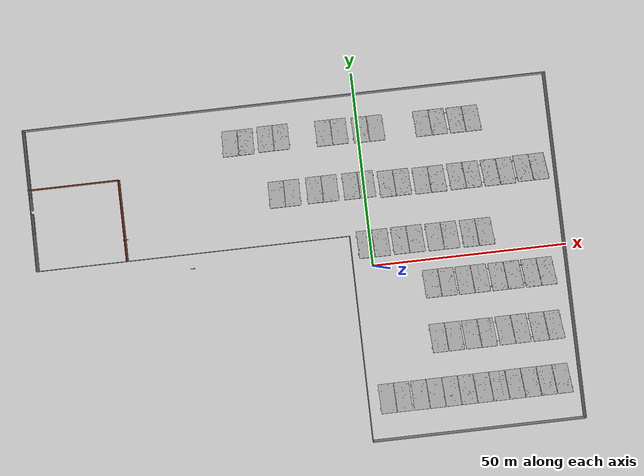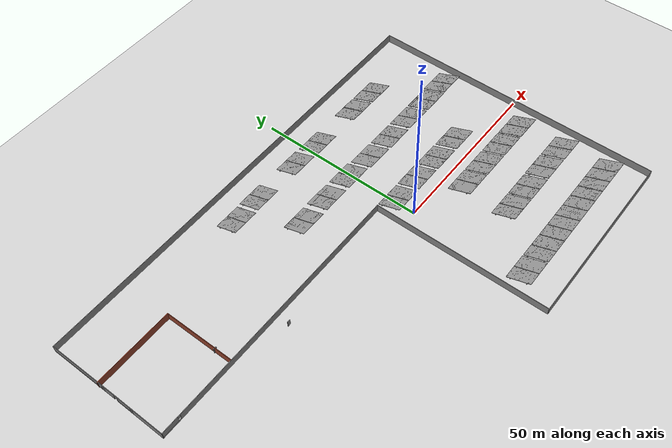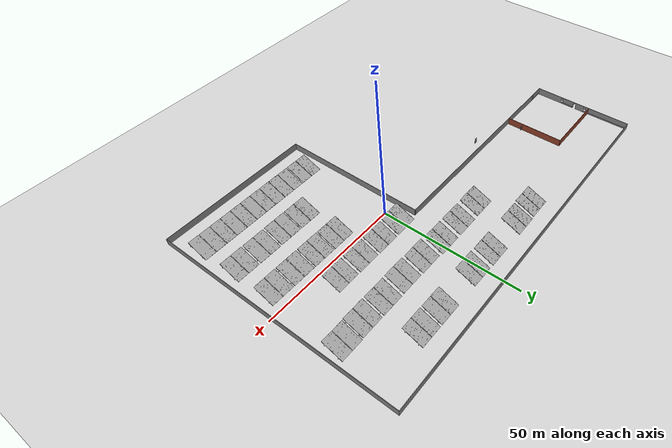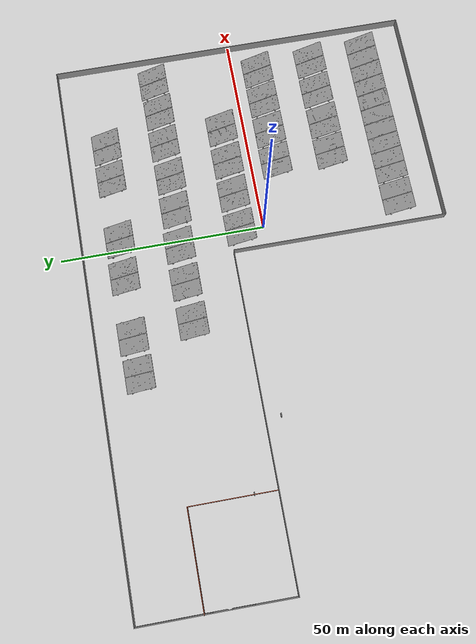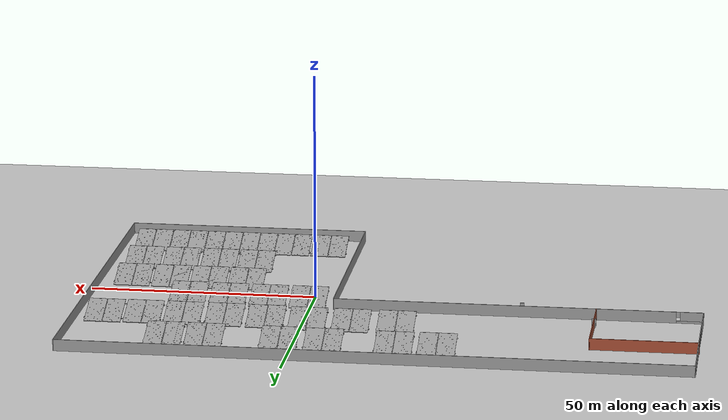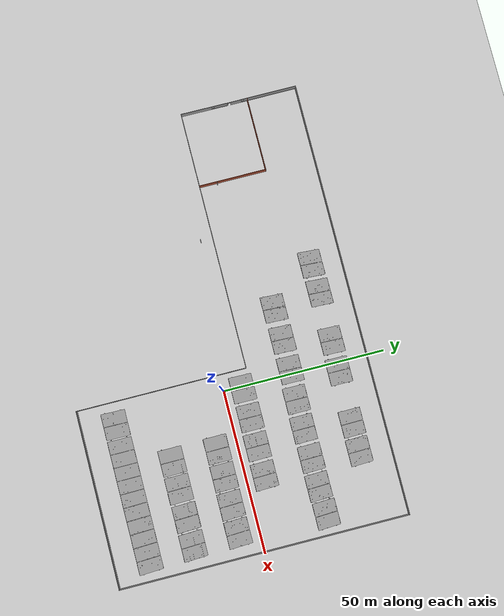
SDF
<sdf version="1.7">
 <world name="default">
  <light name="sun" type="directional">
   <pose>0 0 10 0 -0 0</pose>
   <diffuse>0.8 0.8 0.8 1</diffuse>
   <specular>0.2 0.2 0.2 1</specular>
   <attenuation>
    <range>1000</range>
    <constant>0.9</constant>
    <linear>0.01</linear>
    <quadratic>0.001</quadratic>
   </attenuation>
   <direction>-0.5 0.1 -0.9</direction>
   <spot><inner_angle>0</inner_angle><outer_angle>0</outer_angle><falloff>0</falloff></spot>
  </light>
  <model name="ground_plane">
   <static>1</static>
   <link name="link">
    <collision name="collision">
     <geometry><plane><normal>0 0 1</normal><size>100 100</size></plane></geometry>
     <surface>
      <contact><collide_bitmask>65535</collide_bitmask></contact>
      <friction><ode><mu>100</mu><mu2>50</mu2></ode></friction>
     </surface>
    </collision>
    <visual name="visual">
     <cast_shadows>0</cast_shadows>
     <geometry><plane><normal>0 0 1</normal><size>100 100</size></plane></geometry>
     <material>
      <script><uri>file://media/materials/scripts/gazebo.material</uri><name>Gazebo/Grey</name></script>
     </material>
    </visual>
   </link>
  </model>
  <gravity>0 0 -9.8</gravity>
  <magnetic_field>6e-06 2.3e-05 -4.2e-05</magnetic_field>
  <atmosphere type="adiabatic"/>
  <physics type="ode">
   <max_step_size>0.001</max_step_size>
   <real_time_factor>1</real_time_factor>
   <real_time_update_rate>1000</real_time_update_rate>
  </physics>
  <scene><ambient>0.4 0.4 0.4 1</ambient><background>0.7 0.7 0.7 1</background><shadows>1</shadows></scene>
  <spherical_coordinates>
   <surface_model>EARTH_WGS84</surface_model>
   <latitude_deg>0</latitude_deg>
   <longitude_deg>0</longitude_deg>
   <elevation>0</elevation>
   <heading_deg>0</heading_deg>
  </spherical_coordinates>
  <model name="panelv4">
   <link name="link_0">
    <inertial>
     <mass>1</mass>
     <inertia>
      <ixx>0.166667</ixx>
      <ixy>0</ixy>
      <ixz>0</ixz>
      <iyy>0.166667</iyy>
      <iyz>0</iyz>
      <izz>0.166667</izz>
     </inertia>
    </inertial>
    <pose>0 -0 0 -0.398224 0 0</pose>
    <gravity>0</gravity>
    <visual name="visual">
     <geometry><mesh><uri>model://Panel/panelsolar.obj</uri><scale>0.05 0.05 0.05</scale></mesh></geometry>
     <material>
      <lighting>1</lighting>
      <script><uri>file://media/materials/scripts/gazebo.material</uri><name>Gazebo/Grey</name></script>
      <shader type="pixel"><normal_map>__default__</normal_map></shader>
      <ambient>0.3 0.3 0.3 1</ambient>
      <diffuse>0.7 0.7 0.7 1</diffuse>
      <specular>0.01 0.01 0.01 1</specular>
      <emissive>0 0 0 1</emissive>
     </material>
    </visual>
    <collision name="collision">
     <geometry><mesh><uri>model://Panel/panelsolar.obj</uri><scale>0.05 0.05 0.05</scale></mesh></geometry>
     <surface>
      <friction>
       <ode><mu>1</mu><mu2>1</mu2><fdir1>0 0 0</fdir1><slip1>0</slip1><slip2>0</slip2></ode>
       <torsional>
        <coefficient>1</coefficient>
        <patch_radius>0</patch_radius>
        <surface_radius>0</surface_radius>
        <use_patch_radius>1</use_patch_radius>
        <ode><slip>0</slip></ode>
       </torsional>
      </friction>
      <bounce><restitution_coefficient>0</restitution_coefficient><threshold>1e+06</threshold></bounce>
      <contact>
       <collide_without_contact>0</collide_without_contact>
       <collide_without_contact_bitmask>1</collide_without_contact_bitmask>
       <collide_bitmask>1</collide_bitmask>
       <ode>
        <soft_cfm>0</soft_cfm>
        <soft_erp>0.2</soft_erp>
        <kp>1e+13</kp>
        <kd>1</kd>
        <max_vel>0.01</max_vel>
        <min_depth>0</min_depth>
       </ode>
       <bullet>
        <split_impulse>1</split_impulse>
        <split_impulse_penetration_threshold>-0.01</split_impulse_penetration_threshold>
        <soft_cfm>0</soft_cfm>
        <soft_erp>0.2</soft_erp>
        <kp>1e+13</kp>
        <kd>1</kd>
       </bullet>
      </contact>
     </surface>
    </collision>
   </link>
   <static>1</static>
   <pose>9.55531 -34.0627 1.99863 0 -0 0</pose>
  </model>
  <model name="panelv4_clone">
   <link name="link_0">
    <inertial>
     <mass>1</mass>
     <inertia>
      <ixx>0.166667</ixx>
      <ixy>0</ixy>
      <ixz>0</ixz>
      <iyy>0.166667</iyy>
      <iyz>0</iyz>
      <izz>0.166667</izz>
     </inertia>
    </inertial>
    <pose>0 -0 0 -0.398224 0 0</pose>
    <gravity>0</gravity>
    <visual name="visual">
     <geometry><mesh><uri>model://Panel/panelsolar.obj</uri><scale>0.05 0.05 0.05</scale></mesh></geometry>
     <material>
      <lighting>1</lighting>
      <script><uri>file://media/materials/scripts/gazebo.material</uri><name>Gazebo/Grey</name></script>
      <shader type="pixel"><normal_map>__default__</normal_map></shader>
      <ambient>0.3 0.3 0.3 1</ambient>
      <diffuse>0.7 0.7 0.7 1</diffuse>
      <specular>0.01 0.01 0.01 1</specular>
      <emissive>0 0 0 1</emissive>
     </material>
    </visual>
    <collision name="collision">
     <geometry><mesh><uri>model://Panel/panelsolar.obj</uri><scale>0.05 0.05 0.05</scale></mesh></geometry>
     <surface>
      <friction>
       <ode><mu>1</mu><mu2>1</mu2><fdir1>0 0 0</fdir1><slip1>0</slip1><slip2>0</slip2></ode>
       <torsional>
        <coefficient>1</coefficient>
        <patch_radius>0</patch_radius>
        <surface_radius>0</surface_radius>
        <use_patch_radius>1</use_patch_radius>
        <ode><slip>0</slip></ode>
       </torsional>
      </friction>
      <bounce><restitution_coefficient>0</restitution_coefficient><threshold>1e+06</threshold></bounce>
      <contact>
       <collide_without_contact>0</collide_without_contact>
       <collide_without_contact_bitmask>1</collide_without_contact_bitmask>
       <collide_bitmask>1</collide_bitmask>
       <ode>
        <soft_cfm>0</soft_cfm>
        <soft_erp>0.2</soft_erp>
        <kp>1e+13</kp>
        <kd>1</kd>
        <max_vel>0.01</max_vel>
        <min_depth>0</min_depth>
       </ode>
       <bullet>
        <split_impulse>1</split_impulse>
        <split_impulse_penetration_threshold>-0.01</split_impulse_penetration_threshold>
        <soft_cfm>0</soft_cfm>
        <soft_erp>0.2</soft_erp>
        <kp>1e+13</kp>
        <kd>1</kd>
       </bullet>
      </contact>
     </surface>
    </collision>
   </link>
   <static>1</static>
   <pose>42 -34 2 0 -0 0</pose>
  </model>
  <model name="panelv4_clone_0">
   <link name="link_0">
    <inertial>
     <mass>1</mass>
     <inertia>
      <ixx>0.166667</ixx>
      <ixy>0</ixy>
      <ixz>0</ixz>
      <iyy>0.166667</iyy>
      <iyz>0</iyz>
      <izz>0.166667</izz>
     </inertia>
    </inertial>
    <pose>0 -0 0 -0.398224 0 0</pose>
    <gravity>0</gravity>
    <visual name="visual">
     <geometry><mesh><uri>model://Panel/panelsolar.obj</uri><scale>0.05 0.05 0.05</scale></mesh></geometry>
     <material>
      <lighting>1</lighting>
      <script><uri>file://media/materials/scripts/gazebo.material</uri><name>Gazebo/Grey</name></script>
      <shader type="pixel"><normal_map>__default__</normal_map></shader>
      <ambient>0.3 0.3 0.3 1</ambient>
      <diffuse>0.7 0.7 0.7 1</diffuse>
      <specular>0.01 0.01 0.01 1</specular>
      <emissive>0 0 0 1</emissive>
     </material>
    </visual>
    <collision name="collision">
     <geometry><mesh><uri>model://Panel/panelsolar.obj</uri><scale>0.05 0.05 0.05</scale></mesh></geometry>
     <surface>
      <friction>
       <ode><mu>1</mu><mu2>1</mu2><fdir1>0 0 0</fdir1><slip1>0</slip1><slip2>0</slip2></ode>
       <torsional>
        <coefficient>1</coefficient>
        <patch_radius>0</patch_radius>
        <surface_radius>0</surface_radius>
        <use_patch_radius>1</use_patch_radius>
        <ode><slip>0</slip></ode>
       </torsional>
      </friction>
      <bounce><restitution_coefficient>0</restitution_coefficient><threshold>1e+06</threshold></bounce>
      <contact>
       <collide_without_contact>0</collide_without_contact>
       <collide_without_contact_bitmask>1</collide_without_contact_bitmask>
       <collide_bitmask>1</collide_bitmask>
       <ode>
        <soft_cfm>0</soft_cfm>
        <soft_erp>0.2</soft_erp>
        <kp>1e+13</kp>
        <kd>1</kd>
        <max_vel>0.01</max_vel>
        <min_depth>0</min_depth>
       </ode>
       <bullet>
        <split_impulse>1</split_impulse>
        <split_impulse_penetration_threshold>-0.01</split_impulse_penetration_threshold>
        <soft_cfm>0</soft_cfm>
        <soft_erp>0.2</soft_erp>
        <kp>1e+13</kp>
        <kd>1</kd>
       </bullet>
      </contact>
     </surface>
    </collision>
   </link>
   <static>1</static>
   <pose>24.2399 -6.34265 1.99863 0 -0 0</pose>
  </model>
  <model name="panelv4_clone_1">
   <link name="link_0">
    <inertial>
     <mass>1</mass>
     <inertia>
      <ixx>0.166667</ixx>
      <ixy>0</ixy>
      <ixz>0</ixz>
      <iyy>0.166667</iyy>
      <iyz>0</iyz>
      <izz>0.166667</izz>
     </inertia>
    </inertial>
    <pose>0 -0 0 -0.398224 0 0</pose>
    <gravity>0</gravity>
    <visual name="visual">
     <geometry><mesh><uri>model://Panel/panelsolar.obj</uri><scale>0.05 0.05 0.05</scale></mesh></geometry>
     <material>
      <lighting>1</lighting>
      <script><uri>file://media/materials/scripts/gazebo.material</uri><name>Gazebo/Grey</name></script>
      <shader type="pixel"><normal_map>__default__</normal_map></shader>
      <ambient>0.3 0.3 0.3 1</ambient>
      <diffuse>0.7 0.7 0.7 1</diffuse>
      <specular>0.01 0.01 0.01 1</specular>
      <emissive>0 0 0 1</emissive>
     </material>
    </visual>
    <collision name="collision">
     <geometry><mesh><uri>model://Panel/panelsolar.obj</uri><scale>0.05 0.05 0.05</scale></mesh></geometry>
     <surface>
      <friction>
       <ode><mu>1</mu><mu2>1</mu2><fdir1>0 0 0</fdir1><slip1>0</slip1><slip2>0</slip2></ode>
       <torsional>
        <coefficient>1</coefficient>
        <patch_radius>0</patch_radius>
        <surface_radius>0</surface_radius>
        <use_patch_radius>1</use_patch_radius>
        <ode><slip>0</slip></ode>
       </torsional>
      </friction>
      <bounce><restitution_coefficient>0</restitution_coefficient><threshold>1e+06</threshold></bounce>
      <contact>
       <collide_without_contact>0</collide_without_contact>
       <collide_without_contact_bitmask>1</collide_without_contact_bitmask>
       <collide_bitmask>1</collide_bitmask>
       <ode>
        <soft_cfm>0</soft_cfm>
        <soft_erp>0.2</soft_erp>
        <kp>1e+13</kp>
        <kd>1</kd>
        <max_vel>0.01</max_vel>
        <min_depth>0</min_depth>
       </ode>
       <bullet>
        <split_impulse>1</split_impulse>
        <split_impulse_penetration_threshold>-0.01</split_impulse_penetration_threshold>
        <soft_cfm>0</soft_cfm>
        <soft_erp>0.2</soft_erp>
        <kp>1e+13</kp>
        <kd>1</kd>
       </bullet>
      </contact>
     </surface>
    </collision>
   </link>
   <static>1</static>
   <pose>32.7705 -6.37698 1.99863 0 -0 0</pose>
  </model>
  <model name="panelv4_clone_2">
   <link name="link_0">
    <inertial>
     <mass>1</mass>
     <inertia>
      <ixx>0.166667</ixx>
      <ixy>0</ixy>
      <ixz>0</ixz>
      <iyy>0.166667</iyy>
      <iyz>0</iyz>
      <izz>0.166667</izz>
     </inertia>
    </inertial>
    <pose>0 -0 0 -0.398224 0 0</pose>
    <gravity>0</gravity>
    <visual name="visual">
     <geometry><mesh><uri>model://Panel/panelsolar.obj</uri><scale>0.05 0.05 0.05</scale></mesh></geometry>
     <material>
      <lighting>1</lighting>
      <script><uri>file://media/materials/scripts/gazebo.material</uri><name>Gazebo/Grey</name></script>
      <shader type="pixel"><normal_map>__default__</normal_map></shader>
      <ambient>0.3 0.3 0.3 1</ambient>
      <diffuse>0.7 0.7 0.7 1</diffuse>
      <specular>0.01 0.01 0.01 1</specular>
      <emissive>0 0 0 1</emissive>
     </material>
    </visual>
    <collision name="collision">
     <geometry><mesh><uri>model://Panel/panelsolar.obj</uri><scale>0.05 0.05 0.05</scale></mesh></geometry>
     <surface>
      <friction>
       <ode><mu>1</mu><mu2>1</mu2><fdir1>0 0 0</fdir1><slip1>0</slip1><slip2>0</slip2></ode>
       <torsional>
        <coefficient>1</coefficient>
        <patch_radius>0</patch_radius>
        <surface_radius>0</surface_radius>
        <use_patch_radius>1</use_patch_radius>
        <ode><slip>0</slip></ode>
       </torsional>
      </friction>
      <bounce><restitution_coefficient>0</restitution_coefficient><threshold>1e+06</threshold></bounce>
      <contact>
       <collide_without_contact>0</collide_without_contact>
       <collide_without_contact_bitmask>1</collide_without_contact_bitmask>
       <collide_bitmask>1</collide_bitmask>
       <ode>
        <soft_cfm>0</soft_cfm>
        <soft_erp>0.2</soft_erp>
        <kp>1e+13</kp>
        <kd>1</kd>
        <max_vel>0.01</max_vel>
        <min_depth>0</min_depth>
       </ode>
       <bullet>
        <split_impulse>1</split_impulse>
        <split_impulse_penetration_threshold>-0.01</split_impulse_penetration_threshold>
        <soft_cfm>0</soft_cfm>
        <soft_erp>0.2</soft_erp>
        <kp>1e+13</kp>
        <kd>1</kd>
       </bullet>
      </contact>
     </surface>
    </collision>
   </link>
   <static>1</static>
   <pose>24.345 -20.2567 1.99863 0 -0 0</pose>
  </model>
  <model name="panelv4_clone_3">
   <link name="link_0">
    <inertial>
     <mass>1</mass>
     <inertia>
      <ixx>0.166667</ixx>
      <ixy>0</ixy>
      <ixz>0</ixz>
      <iyy>0.166667</iyy>
      <iyz>0</iyz>
      <izz>0.166667</izz>
     </inertia>
    </inertial>
    <pose>0 -0 0 -0.398224 0 0</pose>
    <gravity>0</gravity>
    <visual name="visual">
     <geometry><mesh><uri>model://Panel/panelsolar.obj</uri><scale>0.05 0.05 0.05</scale></mesh></geometry>
     <material>
      <lighting>1</lighting>
      <script><uri>file://media/materials/scripts/gazebo.material</uri><name>Gazebo/Grey</name></script>
      <shader type="pixel"><normal_map>__default__</normal_map></shader>
      <ambient>0.3 0.3 0.3 1</ambient>
      <diffuse>0.7 0.7 0.7 1</diffuse>
      <specular>0.01 0.01 0.01 1</specular>
      <emissive>0 0 0 1</emissive>
     </material>
    </visual>
    <collision name="collision">
     <geometry><mesh><uri>model://Panel/panelsolar.obj</uri><scale>0.05 0.05 0.05</scale></mesh></geometry>
     <surface>
      <friction>
       <ode><mu>1</mu><mu2>1</mu2><fdir1>0 0 0</fdir1><slip1>0</slip1><slip2>0</slip2></ode>
       <torsional>
        <coefficient>1</coefficient>
        <patch_radius>0</patch_radius>
        <surface_radius>0</surface_radius>
        <use_patch_radius>1</use_patch_radius>
        <ode><slip>0</slip></ode>
       </torsional>
      </friction>
      <bounce><restitution_coefficient>0</restitution_coefficient><threshold>1e+06</threshold></bounce>
      <contact>
       <collide_without_contact>0</collide_without_contact>
       <collide_without_contact_bitmask>1</collide_without_contact_bitmask>
       <collide_bitmask>1</collide_bitmask>
       <ode>
        <soft_cfm>0</soft_cfm>
        <soft_erp>0.2</soft_erp>
        <kp>1e+13</kp>
        <kd>1</kd>
        <max_vel>0.01</max_vel>
        <min_depth>0</min_depth>
       </ode>
       <bullet>
        <split_impulse>1</split_impulse>
        <split_impulse_penetration_threshold>-0.01</split_impulse_penetration_threshold>
        <soft_cfm>0</soft_cfm>
        <soft_erp>0.2</soft_erp>
        <kp>1e+13</kp>
        <kd>1</kd>
       </bullet>
      </contact>
     </surface>
    </collision>
   </link>
   <static>1</static>
   <pose>33.8775 -34.0033 1.99863 0 -0 0</pose>
  </model>
  <model name="panelv4_clone_4">
   <link name="link_0">
    <inertial>
     <mass>1</mass>
     <inertia>
      <ixx>0.166667</ixx>
      <ixy>0</ixy>
      <ixz>0</ixz>
      <iyy>0.166667</iyy>
      <iyz>0</iyz>
      <izz>0.166667</izz>
     </inertia>
    </inertial>
    <pose>0 -0 0 -0.398224 0 0</pose>
    <gravity>0</gravity>
    <visual name="visual">
     <geometry><mesh><uri>model://Panel/panelsolar.obj</uri><scale>0.05 0.05 0.05</scale></mesh></geometry>
     <material>
      <lighting>1</lighting>
      <script><uri>file://media/materials/scripts/gazebo.material</uri><name>Gazebo/Grey</name></script>
      <shader type="pixel"><normal_map>__default__</normal_map></shader>
      <ambient>0.3 0.3 0.3 1</ambient>
      <diffuse>0.7 0.7 0.7 1</diffuse>
      <specular>0.01 0.01 0.01 1</specular>
      <emissive>0 0 0 1</emissive>
     </material>
    </visual>
    <collision name="collision">
     <geometry><mesh><uri>model://Panel/panelsolar.obj</uri><scale>0.05 0.05 0.05</scale></mesh></geometry>
     <surface>
      <friction>
       <ode><mu>1</mu><mu2>1</mu2><fdir1>0 0 0</fdir1><slip1>0</slip1><slip2>0</slip2></ode>
       <torsional>
        <coefficient>1</coefficient>
        <patch_radius>0</patch_radius>
        <surface_radius>0</surface_radius>
        <use_patch_radius>1</use_patch_radius>
        <ode><slip>0</slip></ode>
       </torsional>
      </friction>
      <bounce><restitution_coefficient>0</restitution_coefficient><threshold>1e+06</threshold></bounce>
      <contact>
       <collide_without_contact>0</collide_without_contact>
       <collide_without_contact_bitmask>1</collide_without_contact_bitmask>
       <collide_bitmask>1</collide_bitmask>
       <ode>
        <soft_cfm>0</soft_cfm>
        <soft_erp>0.2</soft_erp>
        <kp>1e+13</kp>
        <kd>1</kd>
        <max_vel>0.01</max_vel>
        <min_depth>0</min_depth>
       </ode>
       <bullet>
        <split_impulse>1</split_impulse>
        <split_impulse_penetration_threshold>-0.01</split_impulse_penetration_threshold>
        <soft_cfm>0</soft_cfm>
        <soft_erp>0.2</soft_erp>
        <kp>1e+13</kp>
        <kd>1</kd>
       </bullet>
      </contact>
     </surface>
    </collision>
   </link>
   <static>1</static>
   <pose>25.738 -34.035 1.99863 0 -0 0</pose>
  </model>
  <model name="panelv4_clone_5">
   <link name="link_0">
    <inertial>
     <mass>1</mass>
     <inertia>
      <ixx>0.166667</ixx>
      <ixy>0</ixy>
      <ixz>0</ixz>
      <iyy>0.166667</iyy>
      <iyz>0</iyz>
      <izz>0.166667</izz>
     </inertia>
    </inertial>
    <pose>0 -0 0 -0.398224 0 0</pose>
    <gravity>0</gravity>
    <visual name="visual">
     <geometry><mesh><uri>model://Panel/panelsolar.obj</uri><scale>0.05 0.05 0.05</scale></mesh></geometry>
     <material>
      <lighting>1</lighting>
      <script><uri>file://media/materials/scripts/gazebo.material</uri><name>Gazebo/Grey</name></script>
      <shader type="pixel"><normal_map>__default__</normal_map></shader>
      <ambient>0.3 0.3 0.3 1</ambient>
      <diffuse>0.7 0.7 0.7 1</diffuse>
      <specular>0.01 0.01 0.01 1</specular>
      <emissive>0 0 0 1</emissive>
     </material>
    </visual>
    <collision name="collision">
     <geometry><mesh><uri>model://Panel/panelsolar.obj</uri><scale>0.05 0.05 0.05</scale></mesh></geometry>
     <surface>
      <friction>
       <ode><mu>1</mu><mu2>1</mu2><fdir1>0 0 0</fdir1><slip1>0</slip1><slip2>0</slip2></ode>
       <torsional>
        <coefficient>1</coefficient>
        <patch_radius>0</patch_radius>
        <surface_radius>0</surface_radius>
        <use_patch_radius>1</use_patch_radius>
        <ode><slip>0</slip></ode>
       </torsional>
      </friction>
      <bounce><restitution_coefficient>0</restitution_coefficient><threshold>1e+06</threshold></bounce>
      <contact>
       <collide_without_contact>0</collide_without_contact>
       <collide_without_contact_bitmask>1</collide_without_contact_bitmask>
       <collide_bitmask>1</collide_bitmask>
       <ode>
        <soft_cfm>0</soft_cfm>
        <soft_erp>0.2</soft_erp>
        <kp>1e+13</kp>
        <kd>1</kd>
        <max_vel>0.01</max_vel>
        <min_depth>0</min_depth>
       </ode>
       <bullet>
        <split_impulse>1</split_impulse>
        <split_impulse_penetration_threshold>-0.01</split_impulse_penetration_threshold>
        <soft_cfm>0</soft_cfm>
        <soft_erp>0.2</soft_erp>
        <kp>1e+13</kp>
        <kd>1</kd>
       </bullet>
      </contact>
     </surface>
    </collision>
   </link>
   <static>1</static>
   <pose>17.6278 -34.0474 1.99863 0 -0 0</pose>
  </model>
  <model name="panelv4_clone_6">
   <link name="link_0">
    <inertial>
     <mass>1</mass>
     <inertia>
      <ixx>0.166667</ixx>
      <ixy>0</ixy>
      <ixz>0</ixz>
      <iyy>0.166667</iyy>
      <iyz>0</iyz>
      <izz>0.166667</izz>
     </inertia>
    </inertial>
    <pose>0 -0 0 -0.398224 0 0</pose>
    <gravity>0</gravity>
    <visual name="visual">
     <geometry><mesh><uri>model://Panel/panelsolar.obj</uri><scale>0.05 0.05 0.05</scale></mesh></geometry>
     <material>
      <lighting>1</lighting>
      <script><uri>file://media/materials/scripts/gazebo.material</uri><name>Gazebo/Grey</name></script>
      <shader type="pixel"><normal_map>__default__</normal_map></shader>
      <ambient>0.3 0.3 0.3 1</ambient>
      <diffuse>0.7 0.7 0.7 1</diffuse>
      <specular>0.01 0.01 0.01 1</specular>
      <emissive>0 0 0 1</emissive>
     </material>
    </visual>
    <collision name="collision">
     <geometry><mesh><uri>model://Panel/panelsolar.obj</uri><scale>0.05 0.05 0.05</scale></mesh></geometry>
     <surface>
      <friction>
       <ode><mu>1</mu><mu2>1</mu2><fdir1>0 0 0</fdir1><slip1>0</slip1><slip2>0</slip2></ode>
       <torsional>
        <coefficient>1</coefficient>
        <patch_radius>0</patch_radius>
        <surface_radius>0</surface_radius>
        <use_patch_radius>1</use_patch_radius>
        <ode><slip>0</slip></ode>
       </torsional>
      </friction>
      <bounce><restitution_coefficient>0</restitution_coefficient><threshold>1e+06</threshold></bounce>
      <contact>
       <collide_without_contact>0</collide_without_contact>
       <collide_without_contact_bitmask>1</collide_without_contact_bitmask>
       <collide_bitmask>1</collide_bitmask>
       <ode>
        <soft_cfm>0</soft_cfm>
        <soft_erp>0.2</soft_erp>
        <kp>1e+13</kp>
        <kd>1</kd>
        <max_vel>0.01</max_vel>
        <min_depth>0</min_depth>
       </ode>
       <bullet>
        <split_impulse>1</split_impulse>
        <split_impulse_penetration_threshold>-0.01</split_impulse_penetration_threshold>
        <soft_cfm>0</soft_cfm>
        <soft_erp>0.2</soft_erp>
        <kp>1e+13</kp>
        <kd>1</kd>
       </bullet>
      </contact>
     </surface>
    </collision>
   </link>
   <static>1</static>
   <pose>15.7973 -6.29418 1.99863 0 -0 0</pose>
  </model>
  <model name="panelv4_clone_7">
   <link name="link_0">
    <inertial>
     <mass>1</mass>
     <inertia>
      <ixx>0.166667</ixx>
      <ixy>0</ixy>
      <ixz>0</ixz>
      <iyy>0.166667</iyy>
      <iyz>0</iyz>
      <izz>0.166667</izz>
     </inertia>
    </inertial>
    <pose>0 -0 0 -0.398224 0 0</pose>
    <gravity>0</gravity>
    <visual name="visual">
     <geometry><mesh><uri>model://Panel/panelsolar.obj</uri><scale>0.05 0.05 0.05</scale></mesh></geometry>
     <material>
      <lighting>1</lighting>
      <script><uri>file://media/materials/scripts/gazebo.material</uri><name>Gazebo/Grey</name></script>
      <shader type="pixel"><normal_map>__default__</normal_map></shader>
      <ambient>0.3 0.3 0.3 1</ambient>
      <diffuse>0.7 0.7 0.7 1</diffuse>
      <specular>0.01 0.01 0.01 1</specular>
      <emissive>0 0 0 1</emissive>
     </material>
    </visual>
    <collision name="collision">
     <geometry><mesh><uri>model://Panel/panelsolar.obj</uri><scale>0.05 0.05 0.05</scale></mesh></geometry>
     <surface>
      <friction>
       <ode><mu>1</mu><mu2>1</mu2><fdir1>0 0 0</fdir1><slip1>0</slip1><slip2>0</slip2></ode>
       <torsional>
        <coefficient>1</coefficient>
        <patch_radius>0</patch_radius>
        <surface_radius>0</surface_radius>
        <use_patch_radius>1</use_patch_radius>
        <ode><slip>0</slip></ode>
       </torsional>
      </friction>
      <bounce><restitution_coefficient>0</restitution_coefficient><threshold>1e+06</threshold></bounce>
      <contact>
       <collide_without_contact>0</collide_without_contact>
       <collide_without_contact_bitmask>1</collide_without_contact_bitmask>
       <collide_bitmask>1</collide_bitmask>
       <ode>
        <soft_cfm>0</soft_cfm>
        <soft_erp>0.2</soft_erp>
        <kp>1e+13</kp>
        <kd>1</kd>
        <max_vel>0.01</max_vel>
        <min_depth>0</min_depth>
       </ode>
       <bullet>
        <split_impulse>1</split_impulse>
        <split_impulse_penetration_threshold>-0.01</split_impulse_penetration_threshold>
        <soft_cfm>0</soft_cfm>
        <soft_erp>0.2</soft_erp>
        <kp>1e+13</kp>
        <kd>1</kd>
       </bullet>
      </contact>
     </surface>
    </collision>
   </link>
   <static>1</static>
   <pose>41.2539 -6.40936 1.99863 0 -0 0</pose>
  </model>
  <model name="panelv4_clone_8">
   <link name="link_0">
    <inertial>
     <mass>1</mass>
     <inertia>
      <ixx>0.166667</ixx>
      <ixy>0</ixy>
      <ixz>0</ixz>
      <iyy>0.166667</iyy>
      <iyz>0</iyz>
      <izz>0.166667</izz>
     </inertia>
    </inertial>
    <pose>0 -0 0 -0.398224 0 0</pose>
    <gravity>0</gravity>
    <visual name="visual">
     <geometry><mesh><uri>model://Panel/panelsolar.obj</uri><scale>0.05 0.05 0.05</scale></mesh></geometry>
     <material>
      <lighting>1</lighting>
      <script><uri>file://media/materials/scripts/gazebo.material</uri><name>Gazebo/Grey</name></script>
      <shader type="pixel"><normal_map>__default__</normal_map></shader>
      <ambient>0.3 0.3 0.3 1</ambient>
      <diffuse>0.7 0.7 0.7 1</diffuse>
      <specular>0.01 0.01 0.01 1</specular>
      <emissive>0 0 0 1</emissive>
     </material>
    </visual>
    <collision name="collision">
     <geometry><mesh><uri>model://Panel/panelsolar.obj</uri><scale>0.05 0.05 0.05</scale></mesh></geometry>
     <surface>
      <friction>
       <ode><mu>1</mu><mu2>1</mu2><fdir1>0 0 0</fdir1><slip1>0</slip1><slip2>0</slip2></ode>
       <torsional>
        <coefficient>1</coefficient>
        <patch_radius>0</patch_radius>
        <surface_radius>0</surface_radius>
        <use_patch_radius>1</use_patch_radius>
        <ode><slip>0</slip></ode>
       </torsional>
      </friction>
      <bounce><restitution_coefficient>0</restitution_coefficient><threshold>1e+06</threshold></bounce>
      <contact>
       <collide_without_contact>0</collide_without_contact>
       <collide_without_contact_bitmask>1</collide_without_contact_bitmask>
       <collide_bitmask>1</collide_bitmask>
       <ode>
        <soft_cfm>0</soft_cfm>
        <soft_erp>0.2</soft_erp>
        <kp>1e+13</kp>
        <kd>1</kd>
        <max_vel>0.01</max_vel>
        <min_depth>0</min_depth>
       </ode>
       <bullet>
        <split_impulse>1</split_impulse>
        <split_impulse_penetration_threshold>-0.01</split_impulse_penetration_threshold>
        <soft_cfm>0</soft_cfm>
        <soft_erp>0.2</soft_erp>
        <kp>1e+13</kp>
        <kd>1</kd>
       </bullet>
      </contact>
     </surface>
    </collision>
   </link>
   <static>1</static>
   <pose>15.9212 -20.2278 1.99863 0 -0 0</pose>
  </model>
  <model name="panelv4_clone_9">
   <link name="link_0">
    <inertial>
     <mass>1</mass>
     <inertia>
      <ixx>0.166667</ixx>
      <ixy>0</ixy>
      <ixz>0</ixz>
      <iyy>0.166667</iyy>
      <iyz>0</iyz>
      <izz>0.166667</izz>
     </inertia>
    </inertial>
    <pose>0 -0 0 -0.398224 0 0</pose>
    <gravity>0</gravity>
    <visual name="visual">
     <geometry><mesh><uri>model://Panel/panelsolar.obj</uri><scale>0.05 0.05 0.05</scale></mesh></geometry>
     <material>
      <lighting>1</lighting>
      <script><uri>file://media/materials/scripts/gazebo.material</uri><name>Gazebo/Grey</name></script>
      <shader type="pixel"><normal_map>__default__</normal_map></shader>
      <ambient>0.3 0.3 0.3 1</ambient>
      <diffuse>0.7 0.7 0.7 1</diffuse>
      <specular>0.01 0.01 0.01 1</specular>
      <emissive>0 0 0 1</emissive>
     </material>
    </visual>
    <collision name="collision">
     <geometry><mesh><uri>model://Panel/panelsolar.obj</uri><scale>0.05 0.05 0.05</scale></mesh></geometry>
     <surface>
      <friction>
       <ode><mu>1</mu><mu2>1</mu2><fdir1>0 0 0</fdir1><slip1>0</slip1><slip2>0</slip2></ode>
       <torsional>
        <coefficient>1</coefficient>
        <patch_radius>0</patch_radius>
        <surface_radius>0</surface_radius>
        <use_patch_radius>1</use_patch_radius>
        <ode><slip>0</slip></ode>
       </torsional>
      </friction>
      <bounce><restitution_coefficient>0</restitution_coefficient><threshold>1e+06</threshold></bounce>
      <contact>
       <collide_without_contact>0</collide_without_contact>
       <collide_without_contact_bitmask>1</collide_without_contact_bitmask>
       <collide_bitmask>1</collide_bitmask>
       <ode>
        <soft_cfm>0</soft_cfm>
        <soft_erp>0.2</soft_erp>
        <kp>1e+13</kp>
        <kd>1</kd>
        <max_vel>0.01</max_vel>
        <min_depth>0</min_depth>
       </ode>
       <bullet>
        <split_impulse>1</split_impulse>
        <split_impulse_penetration_threshold>-0.01</split_impulse_penetration_threshold>
        <soft_cfm>0</soft_cfm>
        <soft_erp>0.2</soft_erp>
        <kp>1e+13</kp>
        <kd>1</kd>
       </bullet>
      </contact>
     </surface>
    </collision>
   </link>
   <static>1</static>
   <pose>32.9785 -20.202 1.99863 0 -0 0</pose>
  </model>
  <model name="panelv4_clone_10">
   <link name="link_0">
    <inertial>
     <mass>1</mass>
     <inertia>
      <ixx>0.166667</ixx>
      <ixy>0</ixy>
      <ixz>0</ixz>
      <iyy>0.166667</iyy>
      <iyz>0</iyz>
      <izz>0.166667</izz>
     </inertia>
    </inertial>
    <pose>0 -0 0 -0.398224 0 0</pose>
    <gravity>0</gravity>
    <visual name="visual">
     <geometry><mesh><uri>model://Panel/panelsolar.obj</uri><scale>0.05 0.05 0.05</scale></mesh></geometry>
     <material>
      <lighting>1</lighting>
      <script><uri>file://media/materials/scripts/gazebo.material</uri><name>Gazebo/Grey</name></script>
      <shader type="pixel"><normal_map>__default__</normal_map></shader>
      <ambient>0.3 0.3 0.3 1</ambient>
      <diffuse>0.7 0.7 0.7 1</diffuse>
      <specular>0.01 0.01 0.01 1</specular>
      <emissive>0 0 0 1</emissive>
     </material>
    </visual>
    <collision name="collision">
     <geometry><mesh><uri>model://Panel/panelsolar.obj</uri><scale>0.05 0.05 0.05</scale></mesh></geometry>
     <surface>
      <friction>
       <ode><mu>1</mu><mu2>1</mu2><fdir1>0 0 0</fdir1><slip1>0</slip1><slip2>0</slip2></ode>
       <torsional>
        <coefficient>1</coefficient>
        <patch_radius>0</patch_radius>
        <surface_radius>0</surface_radius>
        <use_patch_radius>1</use_patch_radius>
        <ode><slip>0</slip></ode>
       </torsional>
      </friction>
      <bounce><restitution_coefficient>0</restitution_coefficient><threshold>1e+06</threshold></bounce>
      <contact>
       <collide_without_contact>0</collide_without_contact>
       <collide_without_contact_bitmask>1</collide_without_contact_bitmask>
       <collide_bitmask>1</collide_bitmask>
       <ode>
        <soft_cfm>0</soft_cfm>
        <soft_erp>0.2</soft_erp>
        <kp>1e+13</kp>
        <kd>1</kd>
        <max_vel>0.01</max_vel>
        <min_depth>0</min_depth>
       </ode>
       <bullet>
        <split_impulse>1</split_impulse>
        <split_impulse_penetration_threshold>-0.01</split_impulse_penetration_threshold>
        <soft_cfm>0</soft_cfm>
        <soft_erp>0.2</soft_erp>
        <kp>1e+13</kp>
        <kd>1</kd>
       </bullet>
      </contact>
     </surface>
    </collision>
   </link>
   <static>1</static>
   <pose>41.5548 -20.2526 1.99863 0 -0 0</pose>
  </model>
  <model name="panelv4_clone_11">
   <link name="link_0">
    <inertial>
     <mass>1</mass>
     <inertia>
      <ixx>0.166667</ixx>
      <ixy>0</ixy>
      <ixz>0</ixz>
      <iyy>0.166667</iyy>
      <iyz>0</iyz>
      <izz>0.166667</izz>
     </inertia>
    </inertial>
    <pose>0 -0 0 -0.398224 0 0</pose>
    <gravity>0</gravity>
    <visual name="visual">
     <geometry><mesh><uri>model://Panel/panelsolar.obj</uri><scale>0.05 0.05 0.05</scale></mesh></geometry>
     <material>
      <lighting>1</lighting>
      <script><uri>file://media/materials/scripts/gazebo.material</uri><name>Gazebo/Grey</name></script>
      <shader type="pixel"><normal_map>__default__</normal_map></shader>
      <ambient>0.3 0.3 0.3 1</ambient>
      <diffuse>0.7 0.7 0.7 1</diffuse>
      <specular>0.01 0.01 0.01 1</specular>
      <emissive>0 0 0 1</emissive>
     </material>
    </visual>
    <collision name="collision">
     <geometry><mesh><uri>model://Panel/panelsolar.obj</uri><scale>0.05 0.05 0.05</scale></mesh></geometry>
     <surface>
      <friction>
       <ode><mu>1</mu><mu2>1</mu2><fdir1>0 0 0</fdir1><slip1>0</slip1><slip2>0</slip2></ode>
       <torsional>
        <coefficient>1</coefficient>
        <patch_radius>0</patch_radius>
        <surface_radius>0</surface_radius>
        <use_patch_radius>1</use_patch_radius>
        <ode><slip>0</slip></ode>
       </torsional>
      </friction>
      <bounce><restitution_coefficient>0</restitution_coefficient><threshold>1e+06</threshold></bounce>
      <contact>
       <collide_without_contact>0</collide_without_contact>
       <collide_without_contact_bitmask>1</collide_without_contact_bitmask>
       <collide_bitmask>1</collide_bitmask>
       <ode>
        <soft_cfm>0</soft_cfm>
        <soft_erp>0.2</soft_erp>
        <kp>1e+13</kp>
        <kd>1</kd>
        <max_vel>0.01</max_vel>
        <min_depth>0</min_depth>
       </ode>
       <bullet>
        <split_impulse>1</split_impulse>
        <split_impulse_penetration_threshold>-0.01</split_impulse_penetration_threshold>
        <soft_cfm>0</soft_cfm>
        <soft_erp>0.2</soft_erp>
        <kp>1e+13</kp>
        <kd>1</kd>
       </bullet>
      </contact>
     </surface>
    </collision>
   </link>
   <static>1</static>
   <pose>1.14243 -34.0485 1.99863 0 -0 0</pose>
  </model>
  <model name="plantal">
   <pose>-18.1491 0.093328 0 0 -0 0</pose>
   <link name="Wall_0">
    <pose>-67.2498 33.625 0 0 -0 1.5708</pose>
    <visual name="Wall_0_Visual_0">
     <pose>-10.7622 0 1.25 0 -0 0</pose>
     <geometry><box><size>0.225674 0.15 2.5</size></box></geometry>
     <material>
      <script><uri>file://media/materials/scripts/gazebo.material</uri><name>Gazebo/Grey</name></script>
      <ambient>1 1 1 1</ambient>
     </material>
     <meta><layer>0</layer></meta>
    </visual>
    <collision name="Wall_0_Collision_0">
     <geometry><box><size>0.225674 0.15 2.5</size></box></geometry>
     <pose>-10.7622 0 1.25 0 -0 0</pose>
    </collision>
    <visual name="Wall_0_Visual_1">
     <pose>-8.1157 0 1.25 0 -0 0</pose>
     <geometry><box><size>3.26725 0.15 2.5</size></box></geometry>
     <material>
      <script><uri>file://media/materials/scripts/gazebo.material</uri><name>Gazebo/Grey</name></script>
      <ambient>1 1 1 1</ambient>
     </material>
     <meta><layer>0</layer></meta>
    </visual>
    <collision name="Wall_0_Collision_1">
     <geometry><box><size>3.26725 0.15 2.5</size></box></geometry>
     <pose>-8.1157 0 1.25 0 -0 0</pose>
    </collision>
    <visual name="Wall_0_Visual_2">
     <pose>2.19646 0 0.25 0 -0 0</pose>
     <geometry><box><size>17.3571 0.15 0.5</size></box></geometry>
     <material>
      <script><uri>file://media/materials/scripts/gazebo.material</uri><name>Gazebo/Grey</name></script>
      <ambient>1 1 1 1</ambient>
     </material>
     <meta><layer>0</layer></meta>
    </visual>
    <collision name="Wall_0_Collision_2">
     <geometry><box><size>17.3571 0.15 0.5</size></box></geometry>
     <pose>2.19646 0 0.25 0 -0 0</pose>
    </collision>
    <visual name="Wall_0_Visual_3">
     <pose>2.59646 0 1.5 0 -0 0</pose>
     <geometry><box><size>16.5571 0.15 2</size></box></geometry>
     <material>
      <script><uri>file://media/materials/scripts/gazebo.material</uri><name>Gazebo/Grey</name></script>
      <ambient>1 1 1 1</ambient>
     </material>
     <meta><layer>0</layer></meta>
    </visual>
    <collision name="Wall_0_Collision_3">
     <geometry><box><size>16.5571 0.15 2</size></box></geometry>
     <pose>2.59646 0 1.5 0 -0 0</pose>
    </collision>
    <visual name="Wall_0_Visual_4">
     <pose>-6.08208 0 1.9 0 -0 0</pose>
     <geometry><box><size>0.8 0.15 1.2</size></box></geometry>
     <material>
      <script><uri>file://media/materials/scripts/gazebo.material</uri><name>Gazebo/Grey</name></script>
      <ambient>1 1 1 1</ambient>
     </material>
     <meta><layer>0</layer></meta>
    </visual>
    <collision name="Wall_0_Collision_4">
     <geometry><box><size>0.8 0.15 1.2</size></box></geometry>
     <pose>-6.08208 0 1.9 0 -0 0</pose>
    </collision>
    <visual name="Wall_0_Visual_5">
     <pose>-10.1993 0 2.25 0 -0 0</pose>
     <geometry><box><size>0.9 0.15 0.5</size></box></geometry>
     <material>
      <script><uri>file://media/materials/scripts/gazebo.material</uri><name>Gazebo/Grey</name></script>
      <ambient>1 1 1 1</ambient>
     </material>
     <meta><layer>0</layer></meta>
    </visual>
    <collision name="Wall_0_Collision_5">
     <geometry><box><size>0.9 0.15 0.5</size></box></geometry>
     <pose>-10.1993 0 2.25 0 -0 0</pose>
    </collision>
   </link>
   <link name="Wall_1">
    <collision name="Wall_1_Collision">
     <geometry><box><size>134.75 0.15 2.5</size></box></geometry>
     <pose>0 0 1.25 0 -0 0</pose>
    </collision>
    <visual name="Wall_1_Visual">
     <pose>0 0 1.25 0 -0 0</pose>
     <geometry><box><size>134.75 0.15 2.5</size></box></geometry>
     <material>
      <script><uri>file://media/materials/scripts/gazebo.material</uri><name>Gazebo/Grey</name></script>
      <ambient>1 1 1 1</ambient>
     </material>
     <meta><layer>0</layer></meta>
    </visual>
    <pose>0.050249 44.425 0 0 -0 0</pose>
   </link>
   <link name="Wall_2">
    <collision name="Wall_2_Collision">
     <geometry><box><size>89 0.15 2.5</size></box></geometry>
     <pose>0 0 1.25 0 -0 0</pose>
    </collision>
    <visual name="Wall_2_Visual">
     <pose>0 0 1.25 0 -0 0</pose>
     <geometry><box><size>89 0.15 2.5</size></box></geometry>
     <material>
      <script><uri>file://media/materials/scripts/gazebo.material</uri><name>Gazebo/Grey</name></script>
      <ambient>1 1 1 1</ambient>
     </material>
     <meta><layer>0</layer></meta>
    </visual>
    <pose>67.3502 2e-06 0 0 -0 -1.5708</pose>
   </link>
   <link name="Wall_3">
    <collision name="Wall_3_Collision">
     <geometry><box><size>54.5 0.15 2.5</size></box></geometry>
     <pose>0 0 1.25 0 -0 0</pose>
    </collision>
    <visual name="Wall_3_Visual">
     <pose>0 0 1.25 0 -0 0</pose>
     <geometry><box><size>54.5 0.15 2.5</size></box></geometry>
     <material>
      <script><uri>file://media/materials/scripts/gazebo.material</uri><name>Gazebo/Grey</name></script>
      <ambient>1 1 1 1</ambient>
     </material>
     <meta><layer>0</layer></meta>
    </visual>
    <pose>40.1752 -44.425 0 0 -0 3.14159</pose>
   </link>
   <link name="Wall_4">
    <collision name="Wall_4_Collision">
     <geometry><box><size>52.75 0.15 2.5</size></box></geometry>
     <pose>0 0 1.25 0 -0 0</pose>
    </collision>
    <visual name="Wall_4_Visual">
     <pose>0 0 1.25 0 -0 0</pose>
     <geometry><box><size>52.75 0.15 2.5</size></box></geometry>
     <material>
      <script><uri>file://media/materials/scripts/gazebo.material</uri><name>Gazebo/Grey</name></script>
      <ambient>1 1 1 1</ambient>
     </material>
     <meta><layer>0</layer></meta>
    </visual>
    <pose>13.0002 -18.125 0 0 -0 1.5708</pose>
   </link>
   <link name="Wall_5">
    <pose>-27.1747 8.175 0 0 -0 3.14159</pose>
    <visual name="Wall_5_Visual_0">
     <pose>-2.95605 0 1.25 0 -0 0</pose>
     <geometry><box><size>74.5879 0.15 2.5</size></box></geometry>
     <material>
      <script><uri>file://media/materials/scripts/gazebo.material</uri><name>Gazebo/Grey</name></script>
      <ambient>1 1 1 1</ambient>
     </material>
     <meta><layer>0</layer></meta>
    </visual>
    <collision name="Wall_5_Collision_0">
     <geometry><box><size>74.5879 0.15 2.5</size></box></geometry>
     <pose>-2.95605 0 1.25 0 -0 0</pose>
    </collision>
    <visual name="Wall_5_Visual_1">
     <pose>37.2939 0 0.25 0 -0 0</pose>
     <geometry><box><size>5.9121 0.15 0.5</size></box></geometry>
     <material>
      <script><uri>file://media/materials/scripts/gazebo.material</uri><name>Gazebo/Grey</name></script>
      <ambient>1 1 1 1</ambient>
     </material>
     <meta><layer>0</layer></meta>
    </visual>
    <collision name="Wall_5_Collision_1">
     <geometry><box><size>5.9121 0.15 0.5</size></box></geometry>
     <pose>37.2939 0 0.25 0 -0 0</pose>
    </collision>
    <visual name="Wall_5_Visual_2">
     <pose>37.6939 0 1.5 0 -0 0</pose>
     <geometry><box><size>5.1121 0.15 2</size></box></geometry>
     <material>
      <script><uri>file://media/materials/scripts/gazebo.material</uri><name>Gazebo/Grey</name></script>
      <ambient>1 1 1 1</ambient>
     </material>
     <meta><layer>0</layer></meta>
    </visual>
    <collision name="Wall_5_Collision_2">
     <geometry><box><size>5.1121 0.15 2</size></box></geometry>
     <pose>37.6939 0 1.5 0 -0 0</pose>
    </collision>
    <visual name="Wall_5_Visual_3">
     <pose>34.7379 0 1.9 0 -0 0</pose>
     <geometry><box><size>0.8 0.15 1.2</size></box></geometry>
     <material>
      <script><uri>file://media/materials/scripts/gazebo.material</uri><name>Gazebo/Grey</name></script>
      <ambient>1 1 1 1</ambient>
     </material>
     <meta><layer>0</layer></meta>
    </visual>
    <collision name="Wall_5_Collision_3">
     <geometry><box><size>0.8 0.15 1.2</size></box></geometry>
     <pose>34.7379 0 1.9 0 -0 0</pose>
    </collision>
   </link>
   <link name="Wall_6">
    <pose>-67.2998 15.5 0 0 -0 1.56397</pose>
    <visual name="Wall_6_Visual_0">
     <pose>-2.55086 0 1.25 0 -0 0</pose>
     <geometry><box><size>9.69862 0.15 2.5</size></box></geometry>
     <material>
      <script><uri>file://media/materials/scripts/gazebo.material</uri><name>Gazebo/Grey</name></script>
      <ambient>1 1 1 1</ambient>
     </material>
     <meta><layer>0</layer></meta>
    </visual>
    <collision name="Wall_6_Collision_0">
     <geometry><box><size>9.69862 0.15 2.5</size></box></geometry>
     <pose>-2.55086 0 1.25 0 -0 0</pose>
    </collision>
    <visual name="Wall_6_Visual_1">
     <pose>4.84931 0 0.25 0 -0 0</pose>
     <geometry><box><size>5.10172 0.15 0.5</size></box></geometry>
     <material>
      <script><uri>file://media/materials/scripts/gazebo.material</uri><name>Gazebo/Grey</name></script>
      <ambient>1 1 1 1</ambient>
     </material>
     <meta><layer>0</layer></meta>
    </visual>
    <collision name="Wall_6_Collision_1">
     <geometry><box><size>5.10172 0.15 0.5</size></box></geometry>
     <pose>4.84931 0 0.25 0 -0 0</pose>
    </collision>
    <visual name="Wall_6_Visual_2">
     <pose>5.24931 0 1.5 0 -0 0</pose>
     <geometry><box><size>4.30172 0.15 2</size></box></geometry>
     <material>
      <script><uri>file://media/materials/scripts/gazebo.material</uri><name>Gazebo/Grey</name></script>
      <ambient>1 1 1 1</ambient>
     </material>
     <meta><layer>0</layer></meta>
    </visual>
    <collision name="Wall_6_Collision_2">
     <geometry><box><size>4.30172 0.15 2</size></box></geometry>
     <pose>5.24931 0 1.5 0 -0 0</pose>
    </collision>
    <visual name="Wall_6_Visual_3">
     <pose>2.69845 0 1.9 0 -0 0</pose>
     <geometry><box><size>0.8 0.15 1.2</size></box></geometry>
     <material>
      <script><uri>file://media/materials/scripts/gazebo.material</uri><name>Gazebo/Grey</name></script>
      <ambient>1 1 1 1</ambient>
     </material>
     <meta><layer>0</layer></meta>
    </visual>
    <collision name="Wall_6_Collision_3">
     <geometry><box><size>0.8 0.15 1.2</size></box></geometry>
     <pose>2.69845 0 1.9 0 -0 0</pose>
    </collision>
   </link>
   <static>1</static>
  </model>
  <model name="panelv4_clone_6_clone">
   <link name="link_0">
    <inertial>
     <mass>1</mass>
     <inertia>
      <ixx>0.166667</ixx>
      <ixy>0</ixy>
      <ixz>0</ixz>
      <iyy>0.166667</iyy>
      <iyz>0</iyz>
      <izz>0.166667</izz>
     </inertia>
    </inertial>
    <pose>0 -0 0 -0.398224 0 0</pose>
    <gravity>0</gravity>
    <visual name="visual">
     <geometry><mesh><uri>model://Panel/panelsolar.obj</uri><scale>0.05 0.05 0.05</scale></mesh></geometry>
     <material>
      <lighting>1</lighting>
      <script><uri>file://media/materials/scripts/gazebo.material</uri><name>Gazebo/Grey</name></script>
      <shader type="pixel"><normal_map>__default__</normal_map></shader>
      <ambient>0.3 0.3 0.3 1</ambient>
      <diffuse>0.7 0.7 0.7 1</diffuse>
      <specular>0.01 0.01 0.01 1</specular>
      <emissive>0 0 0 1</emissive>
     </material>
    </visual>
    <collision name="collision">
     <geometry><mesh><uri>model://Panel/panelsolar.obj</uri><scale>0.05 0.05 0.05</scale></mesh></geometry>
     <surface>
      <friction>
       <ode><mu>1</mu><mu2>1</mu2><fdir1>0 0 0</fdir1><slip1>0</slip1><slip2>0</slip2></ode>
       <torsional>
        <coefficient>1</coefficient>
        <patch_radius>0</patch_radius>
        <surface_radius>0</surface_radius>
        <use_patch_radius>1</use_patch_radius>
        <ode><slip>0</slip></ode>
       </torsional>
      </friction>
      <bounce><restitution_coefficient>0</restitution_coefficient><threshold>1e+06</threshold></bounce>
      <contact>
       <collide_without_contact>0</collide_without_contact>
       <collide_without_contact_bitmask>1</collide_without_contact_bitmask>
       <collide_bitmask>1</collide_bitmask>
       <ode>
        <soft_cfm>0</soft_cfm>
        <soft_erp>0.2</soft_erp>
        <kp>1e+13</kp>
        <kd>1</kd>
        <max_vel>0.01</max_vel>
        <min_depth>0</min_depth>
       </ode>
       <bullet>
        <split_impulse>1</split_impulse>
        <split_impulse_penetration_threshold>-0.01</split_impulse_penetration_threshold>
        <soft_cfm>0</soft_cfm>
        <soft_erp>0.2</soft_erp>
        <kp>1e+13</kp>
        <kd>1</kd>
       </bullet>
      </contact>
     </surface>
    </collision>
   </link>
   <static>1</static>
   <pose>26.7578 5.4271 1.99863 0 -0 0</pose>
  </model>
  <model name="panelv4_clone_6_clone_0">
   <link name="link_0">
    <inertial>
     <mass>1</mass>
     <inertia>
      <ixx>0.166667</ixx>
      <ixy>0</ixy>
      <ixz>0</ixz>
      <iyy>0.166667</iyy>
      <iyz>0</iyz>
      <izz>0.166667</izz>
     </inertia>
    </inertial>
    <pose>0 -0 0 -0.398224 0 0</pose>
    <gravity>0</gravity>
    <visual name="visual">
     <geometry><mesh><uri>model://Panel/panelsolar.obj</uri><scale>0.05 0.05 0.05</scale></mesh></geometry>
     <material>
      <lighting>1</lighting>
      <script><uri>file://media/materials/scripts/gazebo.material</uri><name>Gazebo/Grey</name></script>
      <shader type="pixel"><normal_map>__default__</normal_map></shader>
      <ambient>0.3 0.3 0.3 1</ambient>
      <diffuse>0.7 0.7 0.7 1</diffuse>
      <specular>0.01 0.01 0.01 1</specular>
      <emissive>0 0 0 1</emissive>
     </material>
    </visual>
    <collision name="collision">
     <geometry><mesh><uri>model://Panel/panelsolar.obj</uri><scale>0.05 0.05 0.05</scale></mesh></geometry>
     <surface>
      <friction>
       <ode><mu>1</mu><mu2>1</mu2><fdir1>0 0 0</fdir1><slip1>0</slip1><slip2>0</slip2></ode>
       <torsional>
        <coefficient>1</coefficient>
        <patch_radius>0</patch_radius>
        <surface_radius>0</surface_radius>
        <use_patch_radius>1</use_patch_radius>
        <ode><slip>0</slip></ode>
       </torsional>
      </friction>
      <bounce><restitution_coefficient>0</restitution_coefficient><threshold>1e+06</threshold></bounce>
      <contact>
       <collide_without_contact>0</collide_without_contact>
       <collide_without_contact_bitmask>1</collide_without_contact_bitmask>
       <collide_bitmask>1</collide_bitmask>
       <ode>
        <soft_cfm>0</soft_cfm>
        <soft_erp>0.2</soft_erp>
        <kp>1e+13</kp>
        <kd>1</kd>
        <max_vel>0.01</max_vel>
        <min_depth>0</min_depth>
       </ode>
       <bullet>
        <split_impulse>1</split_impulse>
        <split_impulse_penetration_threshold>-0.01</split_impulse_penetration_threshold>
        <soft_cfm>0</soft_cfm>
        <soft_erp>0.2</soft_erp>
        <kp>1e+13</kp>
        <kd>1</kd>
       </bullet>
      </contact>
     </surface>
    </collision>
   </link>
   <static>1</static>
   <pose>17.8237 5.49991 1.99863 0 -0 0</pose>
  </model>
  <model name="panelv4_clone_6_clone_1">
   <link name="link_0">
    <inertial>
     <mass>1</mass>
     <inertia>
      <ixx>0.166667</ixx>
      <ixy>0</ixy>
      <ixz>0</ixz>
      <iyy>0.166667</iyy>
      <iyz>0</iyz>
      <izz>0.166667</izz>
     </inertia>
    </inertial>
    <pose>0 -0 0 -0.398224 0 0</pose>
    <gravity>0</gravity>
    <visual name="visual">
     <geometry><mesh><uri>model://Panel/panelsolar.obj</uri><scale>0.05 0.05 0.05</scale></mesh></geometry>
     <material>
      <lighting>1</lighting>
      <script><uri>file://media/materials/scripts/gazebo.material</uri><name>Gazebo/Grey</name></script>
      <shader type="pixel"><normal_map>__default__</normal_map></shader>
      <ambient>0.3 0.3 0.3 1</ambient>
      <diffuse>0.7 0.7 0.7 1</diffuse>
      <specular>0.01 0.01 0.01 1</specular>
      <emissive>0 0 0 1</emissive>
     </material>
    </visual>
    <collision name="collision">
     <geometry><mesh><uri>model://Panel/panelsolar.obj</uri><scale>0.05 0.05 0.05</scale></mesh></geometry>
     <surface>
      <friction>
       <ode><mu>1</mu><mu2>1</mu2><fdir1>0 0 0</fdir1><slip1>0</slip1><slip2>0</slip2></ode>
       <torsional>
        <coefficient>1</coefficient>
        <patch_radius>0</patch_radius>
        <surface_radius>0</surface_radius>
        <use_patch_radius>1</use_patch_radius>
        <ode><slip>0</slip></ode>
       </torsional>
      </friction>
      <bounce><restitution_coefficient>0</restitution_coefficient><threshold>1e+06</threshold></bounce>
      <contact>
       <collide_without_contact>0</collide_without_contact>
       <collide_without_contact_bitmask>1</collide_without_contact_bitmask>
       <collide_bitmask>1</collide_bitmask>
       <ode>
        <soft_cfm>0</soft_cfm>
        <soft_erp>0.2</soft_erp>
        <kp>1e+13</kp>
        <kd>1</kd>
        <max_vel>0.01</max_vel>
        <min_depth>0</min_depth>
       </ode>
       <bullet>
        <split_impulse>1</split_impulse>
        <split_impulse_penetration_threshold>-0.01</split_impulse_penetration_threshold>
        <soft_cfm>0</soft_cfm>
        <soft_erp>0.2</soft_erp>
        <kp>1e+13</kp>
        <kd>1</kd>
       </bullet>
      </contact>
     </surface>
    </collision>
   </link>
   <static>1</static>
   <pose>8.9467 5.58939 1.99863 0 -0 0</pose>
  </model>
  <model name="panelv4_clone_6_clone_2">
   <link name="link_0">
    <inertial>
     <mass>1</mass>
     <inertia>
      <ixx>0.166667</ixx>
      <ixy>0</ixy>
      <ixz>0</ixz>
      <iyy>0.166667</iyy>
      <iyz>0</iyz>
      <izz>0.166667</izz>
     </inertia>
    </inertial>
    <pose>0 -0 0 -0.398224 0 0</pose>
    <gravity>0</gravity>
    <visual name="visual">
     <geometry><mesh><uri>model://Panel/panelsolar.obj</uri><scale>0.05 0.05 0.05</scale></mesh></geometry>
     <material>
      <lighting>1</lighting>
      <script><uri>file://media/materials/scripts/gazebo.material</uri><name>Gazebo/Grey</name></script>
      <shader type="pixel"><normal_map>__default__</normal_map></shader>
      <ambient>0.3 0.3 0.3 1</ambient>
      <diffuse>0.7 0.7 0.7 1</diffuse>
      <specular>0.01 0.01 0.01 1</specular>
      <emissive>0 0 0 1</emissive>
     </material>
    </visual>
    <collision name="collision">
     <geometry><mesh><uri>model://Panel/panelsolar.obj</uri><scale>0.05 0.05 0.05</scale></mesh></geometry>
     <surface>
      <friction>
       <ode><mu>1</mu><mu2>1</mu2><fdir1>0 0 0</fdir1><slip1>0</slip1><slip2>0</slip2></ode>
       <torsional>
        <coefficient>1</coefficient>
        <patch_radius>0</patch_radius>
        <surface_radius>0</surface_radius>
        <use_patch_radius>1</use_patch_radius>
        <ode><slip>0</slip></ode>
       </torsional>
      </friction>
      <bounce><restitution_coefficient>0</restitution_coefficient><threshold>1e+06</threshold></bounce>
      <contact>
       <collide_without_contact>0</collide_without_contact>
       <collide_without_contact_bitmask>1</collide_without_contact_bitmask>
       <collide_bitmask>1</collide_bitmask>
       <ode>
        <soft_cfm>0</soft_cfm>
        <soft_erp>0.2</soft_erp>
        <kp>1e+13</kp>
        <kd>1</kd>
        <max_vel>0.01</max_vel>
        <min_depth>0</min_depth>
       </ode>
       <bullet>
        <split_impulse>1</split_impulse>
        <split_impulse_penetration_threshold>-0.01</split_impulse_penetration_threshold>
        <soft_cfm>0</soft_cfm>
        <soft_erp>0.2</soft_erp>
        <kp>1e+13</kp>
        <kd>1</kd>
       </bullet>
      </contact>
     </surface>
    </collision>
   </link>
   <static>1</static>
   <pose>0.066594 5.54411 1.99863 0 -0 0</pose>
  </model>
  <model name="panelv4_clone_6_clone_0_clone">
   <link name="link_0">
    <inertial>
     <mass>1</mass>
     <inertia>
      <ixx>0.166667</ixx>
      <ixy>0</ixy>
      <ixz>0</ixz>
      <iyy>0.166667</iyy>
      <iyz>0</iyz>
      <izz>0.166667</izz>
     </inertia>
    </inertial>
    <pose>0 -0 0 -0.398224 0 0</pose>
    <gravity>0</gravity>
    <visual name="visual">
     <geometry><mesh><uri>model://Panel/panelsolar.obj</uri><scale>0.05 0.05 0.05</scale></mesh></geometry>
     <material>
      <lighting>1</lighting>
      <script><uri>file://media/materials/scripts/gazebo.material</uri><name>Gazebo/Grey</name></script>
      <shader type="pixel"><normal_map>__default__</normal_map></shader>
      <ambient>0.3 0.3 0.3 1</ambient>
      <diffuse>0.7 0.7 0.7 1</diffuse>
      <specular>0.01 0.01 0.01 1</specular>
      <emissive>0 0 0 1</emissive>
     </material>
    </visual>
    <collision name="collision">
     <geometry><mesh><uri>model://Panel/panelsolar.obj</uri><scale>0.05 0.05 0.05</scale></mesh></geometry>
     <surface>
      <friction>
       <ode><mu>1</mu><mu2>1</mu2><fdir1>0 0 0</fdir1><slip1>0</slip1><slip2>0</slip2></ode>
       <torsional>
        <coefficient>1</coefficient>
        <patch_radius>0</patch_radius>
        <surface_radius>0</surface_radius>
        <use_patch_radius>1</use_patch_radius>
        <ode><slip>0</slip></ode>
       </torsional>
      </friction>
      <bounce><restitution_coefficient>0</restitution_coefficient><threshold>1e+06</threshold></bounce>
      <contact>
       <collide_without_contact>0</collide_without_contact>
       <collide_without_contact_bitmask>1</collide_without_contact_bitmask>
       <collide_bitmask>1</collide_bitmask>
       <ode>
        <soft_cfm>0</soft_cfm>
        <soft_erp>0.2</soft_erp>
        <kp>1e+13</kp>
        <kd>1</kd>
        <max_vel>0.01</max_vel>
        <min_depth>0</min_depth>
       </ode>
       <bullet>
        <split_impulse>1</split_impulse>
        <split_impulse_penetration_threshold>-0.01</split_impulse_penetration_threshold>
        <soft_cfm>0</soft_cfm>
        <soft_erp>0.2</soft_erp>
        <kp>1e+13</kp>
        <kd>1</kd>
       </bullet>
      </contact>
     </surface>
    </collision>
   </link>
   <static>1</static>
   <pose>42.4145 20.4305 1.99863 0 -0 0</pose>
  </model>
  <model name="panelv4_clone_6_clone_0_clone_0">
   <link name="link_0">
    <inertial>
     <mass>1</mass>
     <inertia>
      <ixx>0.166667</ixx>
      <ixy>0</ixy>
      <ixz>0</ixz>
      <iyy>0.166667</iyy>
      <iyz>0</iyz>
      <izz>0.166667</izz>
     </inertia>
    </inertial>
    <pose>0 -0 0 -0.398224 0 0</pose>
    <gravity>0</gravity>
    <visual name="visual">
     <geometry><mesh><uri>model://Panel/panelsolar.obj</uri><scale>0.05 0.05 0.05</scale></mesh></geometry>
     <material>
      <lighting>1</lighting>
      <script><uri>file://media/materials/scripts/gazebo.material</uri><name>Gazebo/Grey</name></script>
      <shader type="pixel"><normal_map>__default__</normal_map></shader>
      <ambient>0.3 0.3 0.3 1</ambient>
      <diffuse>0.7 0.7 0.7 1</diffuse>
      <specular>0.01 0.01 0.01 1</specular>
      <emissive>0 0 0 1</emissive>
     </material>
    </visual>
    <collision name="collision">
     <geometry><mesh><uri>model://Panel/panelsolar.obj</uri><scale>0.05 0.05 0.05</scale></mesh></geometry>
     <surface>
      <friction>
       <ode><mu>1</mu><mu2>1</mu2><fdir1>0 0 0</fdir1><slip1>0</slip1><slip2>0</slip2></ode>
       <torsional>
        <coefficient>1</coefficient>
        <patch_radius>0</patch_radius>
        <surface_radius>0</surface_radius>
        <use_patch_radius>1</use_patch_radius>
        <ode><slip>0</slip></ode>
       </torsional>
      </friction>
      <bounce><restitution_coefficient>0</restitution_coefficient><threshold>1e+06</threshold></bounce>
      <contact>
       <collide_without_contact>0</collide_without_contact>
       <collide_without_contact_bitmask>1</collide_without_contact_bitmask>
       <collide_bitmask>1</collide_bitmask>
       <ode>
        <soft_cfm>0</soft_cfm>
        <soft_erp>0.2</soft_erp>
        <kp>1e+13</kp>
        <kd>1</kd>
        <max_vel>0.01</max_vel>
        <min_depth>0</min_depth>
       </ode>
       <bullet>
        <split_impulse>1</split_impulse>
        <split_impulse_penetration_threshold>-0.01</split_impulse_penetration_threshold>
        <soft_cfm>0</soft_cfm>
        <soft_erp>0.2</soft_erp>
        <kp>1e+13</kp>
        <kd>1</kd>
       </bullet>
      </contact>
     </surface>
    </collision>
   </link>
   <static>1</static>
   <pose>33.924 20.2472 1.99863 0 -0 0</pose>
  </model>
  <model name="panelv4_clone_6_clone_0_clone_1">
   <link name="link_0">
    <inertial>
     <mass>1</mass>
     <inertia>
      <ixx>0.166667</ixx>
      <ixy>0</ixy>
      <ixz>0</ixz>
      <iyy>0.166667</iyy>
      <iyz>0</iyz>
      <izz>0.166667</izz>
     </inertia>
    </inertial>
    <pose>0 -0 0 -0.398224 0 0</pose>
    <gravity>0</gravity>
    <visual name="visual">
     <geometry><mesh><uri>model://Panel/panelsolar.obj</uri><scale>0.05 0.05 0.05</scale></mesh></geometry>
     <material>
      <lighting>1</lighting>
      <script><uri>file://media/materials/scripts/gazebo.material</uri><name>Gazebo/Grey</name></script>
      <shader type="pixel"><normal_map>__default__</normal_map></shader>
      <ambient>0.3 0.3 0.3 1</ambient>
      <diffuse>0.7 0.7 0.7 1</diffuse>
      <specular>0.01 0.01 0.01 1</specular>
      <emissive>0 0 0 1</emissive>
     </material>
    </visual>
    <collision name="collision">
     <geometry><mesh><uri>model://Panel/panelsolar.obj</uri><scale>0.05 0.05 0.05</scale></mesh></geometry>
     <surface>
      <friction>
       <ode><mu>1</mu><mu2>1</mu2><fdir1>0 0 0</fdir1><slip1>0</slip1><slip2>0</slip2></ode>
       <torsional>
        <coefficient>1</coefficient>
        <patch_radius>0</patch_radius>
        <surface_radius>0</surface_radius>
        <use_patch_radius>1</use_patch_radius>
        <ode><slip>0</slip></ode>
       </torsional>
      </friction>
      <bounce><restitution_coefficient>0</restitution_coefficient><threshold>1e+06</threshold></bounce>
      <contact>
       <collide_without_contact>0</collide_without_contact>
       <collide_without_contact_bitmask>1</collide_without_contact_bitmask>
       <collide_bitmask>1</collide_bitmask>
       <ode>
        <soft_cfm>0</soft_cfm>
        <soft_erp>0.2</soft_erp>
        <kp>1e+13</kp>
        <kd>1</kd>
        <max_vel>0.01</max_vel>
        <min_depth>0</min_depth>
       </ode>
       <bullet>
        <split_impulse>1</split_impulse>
        <split_impulse_penetration_threshold>-0.01</split_impulse_penetration_threshold>
        <soft_cfm>0</soft_cfm>
        <soft_erp>0.2</soft_erp>
        <kp>1e+13</kp>
        <kd>1</kd>
       </bullet>
      </contact>
     </surface>
    </collision>
   </link>
   <static>1</static>
   <pose>25.2084 20.2914 1.99863 0 -0 0</pose>
  </model>
  <model name="panelv4_clone_6_clone_0_clone_2">
   <link name="link_0">
    <inertial>
     <mass>1</mass>
     <inertia>
      <ixx>0.166667</ixx>
      <ixy>0</ixy>
      <ixz>0</ixz>
      <iyy>0.166667</iyy>
      <iyz>0</iyz>
      <izz>0.166667</izz>
     </inertia>
    </inertial>
    <pose>0 -0 0 -0.398224 0 0</pose>
    <gravity>0</gravity>
    <visual name="visual">
     <geometry><mesh><uri>model://Panel/panelsolar.obj</uri><scale>0.05 0.05 0.05</scale></mesh></geometry>
     <material>
      <lighting>1</lighting>
      <script><uri>file://media/materials/scripts/gazebo.material</uri><name>Gazebo/Grey</name></script>
      <shader type="pixel"><normal_map>__default__</normal_map></shader>
      <ambient>0.3 0.3 0.3 1</ambient>
      <diffuse>0.7 0.7 0.7 1</diffuse>
      <specular>0.01 0.01 0.01 1</specular>
      <emissive>0 0 0 1</emissive>
     </material>
    </visual>
    <collision name="collision">
     <geometry><mesh><uri>model://Panel/panelsolar.obj</uri><scale>0.05 0.05 0.05</scale></mesh></geometry>
     <surface>
      <friction>
       <ode><mu>1</mu><mu2>1</mu2><fdir1>0 0 0</fdir1><slip1>0</slip1><slip2>0</slip2></ode>
       <torsional>
        <coefficient>1</coefficient>
        <patch_radius>0</patch_radius>
        <surface_radius>0</surface_radius>
        <use_patch_radius>1</use_patch_radius>
        <ode><slip>0</slip></ode>
       </torsional>
      </friction>
      <bounce><restitution_coefficient>0</restitution_coefficient><threshold>1e+06</threshold></bounce>
      <contact>
       <collide_without_contact>0</collide_without_contact>
       <collide_without_contact_bitmask>1</collide_without_contact_bitmask>
       <collide_bitmask>1</collide_bitmask>
       <ode>
        <soft_cfm>0</soft_cfm>
        <soft_erp>0.2</soft_erp>
        <kp>1e+13</kp>
        <kd>1</kd>
        <max_vel>0.01</max_vel>
        <min_depth>0</min_depth>
       </ode>
       <bullet>
        <split_impulse>1</split_impulse>
        <split_impulse_penetration_threshold>-0.01</split_impulse_penetration_threshold>
        <soft_cfm>0</soft_cfm>
        <soft_erp>0.2</soft_erp>
        <kp>1e+13</kp>
        <kd>1</kd>
       </bullet>
      </contact>
     </surface>
    </collision>
   </link>
   <static>1</static>
   <pose>16.1938 20.22 1.99863 0 -0 0</pose>
  </model>
  <model name="panelv4_clone_6_clone_0_clone_3">
   <link name="link_0">
    <inertial>
     <mass>1</mass>
     <inertia>
      <ixx>0.166667</ixx>
      <ixy>0</ixy>
      <ixz>0</ixz>
      <iyy>0.166667</iyy>
      <iyz>0</iyz>
      <izz>0.166667</izz>
     </inertia>
    </inertial>
    <pose>0 -0 0 -0.398224 0 0</pose>
    <gravity>0</gravity>
    <visual name="visual">
     <geometry><mesh><uri>model://Panel/panelsolar.obj</uri><scale>0.05 0.05 0.05</scale></mesh></geometry>
     <material>
      <lighting>1</lighting>
      <script><uri>file://media/materials/scripts/gazebo.material</uri><name>Gazebo/Grey</name></script>
      <shader type="pixel"><normal_map>__default__</normal_map></shader>
      <ambient>0.3 0.3 0.3 1</ambient>
      <diffuse>0.7 0.7 0.7 1</diffuse>
      <specular>0.01 0.01 0.01 1</specular>
      <emissive>0 0 0 1</emissive>
     </material>
    </visual>
    <collision name="collision">
     <geometry><mesh><uri>model://Panel/panelsolar.obj</uri><scale>0.05 0.05 0.05</scale></mesh></geometry>
     <surface>
      <friction>
       <ode><mu>1</mu><mu2>1</mu2><fdir1>0 0 0</fdir1><slip1>0</slip1><slip2>0</slip2></ode>
       <torsional>
        <coefficient>1</coefficient>
        <patch_radius>0</patch_radius>
        <surface_radius>0</surface_radius>
        <use_patch_radius>1</use_patch_radius>
        <ode><slip>0</slip></ode>
       </torsional>
      </friction>
      <bounce><restitution_coefficient>0</restitution_coefficient><threshold>1e+06</threshold></bounce>
      <contact>
       <collide_without_contact>0</collide_without_contact>
       <collide_without_contact_bitmask>1</collide_without_contact_bitmask>
       <collide_bitmask>1</collide_bitmask>
       <ode>
        <soft_cfm>0</soft_cfm>
        <soft_erp>0.2</soft_erp>
        <kp>1e+13</kp>
        <kd>1</kd>
        <max_vel>0.01</max_vel>
        <min_depth>0</min_depth>
       </ode>
       <bullet>
        <split_impulse>1</split_impulse>
        <split_impulse_penetration_threshold>-0.01</split_impulse_penetration_threshold>
        <soft_cfm>0</soft_cfm>
        <soft_erp>0.2</soft_erp>
        <kp>1e+13</kp>
        <kd>1</kd>
       </bullet>
      </contact>
     </surface>
    </collision>
   </link>
   <static>1</static>
   <pose>7.21213 20.3756 1.99863 0 -0 0</pose>
  </model>
  <model name="panelv4_clone_6_clone_0_clone_4">
   <link name="link_0">
    <inertial>
     <mass>1</mass>
     <inertia>
      <ixx>0.166667</ixx>
      <ixy>0</ixy>
      <ixz>0</ixz>
      <iyy>0.166667</iyy>
      <iyz>0</iyz>
      <izz>0.166667</izz>
     </inertia>
    </inertial>
    <pose>0 -0 0 -0.398224 0 0</pose>
    <gravity>0</gravity>
    <visual name="visual">
     <geometry><mesh><uri>model://Panel/panelsolar.obj</uri><scale>0.05 0.05 0.05</scale></mesh></geometry>
     <material>
      <lighting>1</lighting>
      <script><uri>file://media/materials/scripts/gazebo.material</uri><name>Gazebo/Grey</name></script>
      <shader type="pixel"><normal_map>__default__</normal_map></shader>
      <ambient>0.3 0.3 0.3 1</ambient>
      <diffuse>0.7 0.7 0.7 1</diffuse>
      <specular>0.01 0.01 0.01 1</specular>
      <emissive>0 0 0 1</emissive>
     </material>
    </visual>
    <collision name="collision">
     <geometry><mesh><uri>model://Panel/panelsolar.obj</uri><scale>0.05 0.05 0.05</scale></mesh></geometry>
     <surface>
      <friction>
       <ode><mu>1</mu><mu2>1</mu2><fdir1>0 0 0</fdir1><slip1>0</slip1><slip2>0</slip2></ode>
       <torsional>
        <coefficient>1</coefficient>
        <patch_radius>0</patch_radius>
        <surface_radius>0</surface_radius>
        <use_patch_radius>1</use_patch_radius>
        <ode><slip>0</slip></ode>
       </torsional>
      </friction>
      <bounce><restitution_coefficient>0</restitution_coefficient><threshold>1e+06</threshold></bounce>
      <contact>
       <collide_without_contact>0</collide_without_contact>
       <collide_without_contact_bitmask>1</collide_without_contact_bitmask>
       <collide_bitmask>1</collide_bitmask>
       <ode>
        <soft_cfm>0</soft_cfm>
        <soft_erp>0.2</soft_erp>
        <kp>1e+13</kp>
        <kd>1</kd>
        <max_vel>0.01</max_vel>
        <min_depth>0</min_depth>
       </ode>
       <bullet>
        <split_impulse>1</split_impulse>
        <split_impulse_penetration_threshold>-0.01</split_impulse_penetration_threshold>
        <soft_cfm>0</soft_cfm>
        <soft_erp>0.2</soft_erp>
        <kp>1e+13</kp>
        <kd>1</kd>
       </bullet>
      </contact>
     </surface>
    </collision>
   </link>
   <static>1</static>
   <pose>-1.94093 20.8153 1.99863 0 -0 0</pose>
  </model>
  <model name="panelv4_clone_6_clone_0_clone_5">
   <link name="link_0">
    <inertial>
     <mass>1</mass>
     <inertia>
      <ixx>0.166667</ixx>
      <ixy>0</ixy>
      <ixz>0</ixz>
      <iyy>0.166667</iyy>
      <iyz>0</iyz>
      <izz>0.166667</izz>
     </inertia>
    </inertial>
    <pose>0 -0 0 -0.398224 0 0</pose>
    <gravity>0</gravity>
    <visual name="visual">
     <geometry><mesh><uri>model://Panel/panelsolar.obj</uri><scale>0.05 0.05 0.05</scale></mesh></geometry>
     <material>
      <lighting>1</lighting>
      <script><uri>file://media/materials/scripts/gazebo.material</uri><name>Gazebo/Grey</name></script>
      <shader type="pixel"><normal_map>__default__</normal_map></shader>
      <ambient>0.3 0.3 0.3 1</ambient>
      <diffuse>0.7 0.7 0.7 1</diffuse>
      <specular>0.01 0.01 0.01 1</specular>
      <emissive>0 0 0 1</emissive>
     </material>
    </visual>
    <collision name="collision">
     <geometry><mesh><uri>model://Panel/panelsolar.obj</uri><scale>0.05 0.05 0.05</scale></mesh></geometry>
     <surface>
      <friction>
       <ode><mu>1</mu><mu2>1</mu2><fdir1>0 0 0</fdir1><slip1>0</slip1><slip2>0</slip2></ode>
       <torsional>
        <coefficient>1</coefficient>
        <patch_radius>0</patch_radius>
        <surface_radius>0</surface_radius>
        <use_patch_radius>1</use_patch_radius>
        <ode><slip>0</slip></ode>
       </torsional>
      </friction>
      <bounce><restitution_coefficient>0</restitution_coefficient><threshold>1e+06</threshold></bounce>
      <contact>
       <collide_without_contact>0</collide_without_contact>
       <collide_without_contact_bitmask>1</collide_without_contact_bitmask>
       <collide_bitmask>1</collide_bitmask>
       <ode>
        <soft_cfm>0</soft_cfm>
        <soft_erp>0.2</soft_erp>
        <kp>1e+13</kp>
        <kd>1</kd>
        <max_vel>0.01</max_vel>
        <min_depth>0</min_depth>
       </ode>
       <bullet>
        <split_impulse>1</split_impulse>
        <split_impulse_penetration_threshold>-0.01</split_impulse_penetration_threshold>
        <soft_cfm>0</soft_cfm>
        <soft_erp>0.2</soft_erp>
        <kp>1e+13</kp>
        <kd>1</kd>
       </bullet>
      </contact>
     </surface>
    </collision>
   </link>
   <static>1</static>
   <pose>-11.3436 20.8542 1.99863 0 -0 0</pose>
  </model>
  <model name="panelv4_clone_6_clone_0_clone_6">
   <link name="link_0">
    <inertial>
     <mass>1</mass>
     <inertia>
      <ixx>0.166667</ixx>
      <ixy>0</ixy>
      <ixz>0</ixz>
      <iyy>0.166667</iyy>
      <iyz>0</iyz>
      <izz>0.166667</izz>
     </inertia>
    </inertial>
    <pose>0 -0 0 -0.398224 0 0</pose>
    <gravity>0</gravity>
    <visual name="visual">
     <geometry><mesh><uri>model://Panel/panelsolar.obj</uri><scale>0.05 0.05 0.05</scale></mesh></geometry>
     <material>
      <lighting>1</lighting>
      <script><uri>file://media/materials/scripts/gazebo.material</uri><name>Gazebo/Grey</name></script>
      <shader type="pixel"><normal_map>__default__</normal_map></shader>
      <ambient>0.3 0.3 0.3 1</ambient>
      <diffuse>0.7 0.7 0.7 1</diffuse>
      <specular>0.01 0.01 0.01 1</specular>
      <emissive>0 0 0 1</emissive>
     </material>
    </visual>
    <collision name="collision">
     <geometry><mesh><uri>model://Panel/panelsolar.obj</uri><scale>0.05 0.05 0.05</scale></mesh></geometry>
     <surface>
      <friction>
       <ode><mu>1</mu><mu2>1</mu2><fdir1>0 0 0</fdir1><slip1>0</slip1><slip2>0</slip2></ode>
       <torsional>
        <coefficient>1</coefficient>
        <patch_radius>0</patch_radius>
        <surface_radius>0</surface_radius>
        <use_patch_radius>1</use_patch_radius>
        <ode><slip>0</slip></ode>
       </torsional>
      </friction>
      <bounce><restitution_coefficient>0</restitution_coefficient><threshold>1e+06</threshold></bounce>
      <contact>
       <collide_without_contact>0</collide_without_contact>
       <collide_without_contact_bitmask>1</collide_without_contact_bitmask>
       <collide_bitmask>1</collide_bitmask>
       <ode>
        <soft_cfm>0</soft_cfm>
        <soft_erp>0.2</soft_erp>
        <kp>1e+13</kp>
        <kd>1</kd>
        <max_vel>0.01</max_vel>
        <min_depth>0</min_depth>
       </ode>
       <bullet>
        <split_impulse>1</split_impulse>
        <split_impulse_penetration_threshold>-0.01</split_impulse_penetration_threshold>
        <soft_cfm>0</soft_cfm>
        <soft_erp>0.2</soft_erp>
        <kp>1e+13</kp>
        <kd>1</kd>
       </bullet>
      </contact>
     </surface>
    </collision>
   </link>
   <static>1</static>
   <pose>-21.0754 20.771 1.99863 0 -0 0</pose>
  </model>
  <model name="Untitled">
   <pose>-16.8765 18.7696 0 0 -0 0</pose>
   <link name="Door_3">
    <collision name="Door_3_Collision">
     <geometry><box><size>0.9 0.17 2</size></box></geometry>
     <pose>0 0 1 0 -0 0</pose>
    </collision>
    <visual name="Door_3_Visual">
     <pose>0 0 1 0 -0 0</pose>
     <geometry><box><size>0.9 0.17 2</size></box></geometry>
     <material>
      <script><uri>file://media/materials/scripts/gazebo.material</uri><name>Gazebo/Grey</name></script>
     </material>
    </visual>
    <pose>-29.1748 -14.2606 0 0 -0 0</pose>
   </link>
   <link name="Door_4">
    <collision name="Door_4_Collision">
     <geometry><box><size>0.9 0.17 2</size></box></geometry>
     <pose>0 0 1 0 -0 0</pose>
    </collision>
    <visual name="Door_4_Visual">
     <pose>0 0 1 0 -0 0</pose>
     <geometry><box><size>0.9 0.17 2</size></box></geometry>
     <material>
      <script><uri>file://media/materials/scripts/gazebo.material</uri><name>Gazebo/Grey</name></script>
     </material>
    </visual>
    <pose>-45.4363 -4.94987 0 0 -0 0</pose>
   </link>
   <link name="Wall_56">
    <collision name="Wall_56_Collision">
     <geometry><box><size>21 0.15 2.5</size></box></geometry>
     <pose>0 0 1.25 0 -0 0</pose>
    </collision>
    <visual name="Wall_56_Visual">
     <pose>0 0 1.25 0 -0 0</pose>
     <geometry><box><size>21 0.15 2.5</size></box></geometry>
     <material>
      <script><uri>file://media/materials/scripts/gazebo.material</uri><name>Gazebo/Bricks</name></script>
      <ambient>1 1 1 1</ambient>
     </material>
     <meta><layer>0</layer></meta>
    </visual>
    <pose>-45.564 0 0 0 -0 1.5708</pose>
   </link>
   <link name="Wall_57">
    <collision name="Wall_57_Collision">
     <geometry><box><size>23.25 0.15 2.5</size></box></geometry>
     <pose>0 0 1.25 0 -0 0</pose>
    </collision>
    <visual name="Wall_57_Visual">
     <pose>0 0 1.25 0 -0 0</pose>
     <geometry><box><size>23.25 0.15 2.5</size></box></geometry>
     <material>
      <script><uri>file://media/materials/scripts/gazebo.material</uri><name>Gazebo/Bricks</name></script>
      <ambient>1 1 1 1</ambient>
     </material>
     <meta><layer>0</layer></meta>
    </visual>
    <pose>-57.114 10.425 0 0 -0 3.14159</pose>
   </link>
   <static>1</static>
  </model>
  <model name="panelv4_clone_6_clone_0_clone_clone">
   <link name="link_0">
    <inertial>
     <mass>1</mass>
     <inertia>
      <ixx>0.166667</ixx>
      <ixy>0</ixy>
      <ixz>0</ixz>
      <iyy>0.166667</iyy>
      <iyz>0</iyz>
      <izz>0.166667</izz>
     </inertia>
    </inertial>
    <pose>0 -0 0 -0.398224 0 0</pose>
    <gravity>0</gravity>
    <visual name="visual">
     <geometry><mesh><uri>model://Panel/panelsolar.obj</uri><scale>0.05 0.05 0.05</scale></mesh></geometry>
     <material>
      <lighting>1</lighting>
      <script><uri>file://media/materials/scripts/gazebo.material</uri><name>Gazebo/Grey</name></script>
      <shader type="pixel"><normal_map>__default__</normal_map></shader>
      <ambient>0.3 0.3 0.3 1</ambient>
      <diffuse>0.7 0.7 0.7 1</diffuse>
      <specular>0.01 0.01 0.01 1</specular>
      <emissive>0 0 0 1</emissive>
     </material>
    </visual>
    <collision name="collision">
     <geometry><mesh><uri>model://Panel/panelsolar.obj</uri><scale>0.05 0.05 0.05</scale></mesh></geometry>
     <surface>
      <friction>
       <ode><mu>1</mu><mu2>1</mu2><fdir1>0 0 0</fdir1><slip1>0</slip1><slip2>0</slip2></ode>
       <torsional>
        <coefficient>1</coefficient>
        <patch_radius>0</patch_radius>
        <surface_radius>0</surface_radius>
        <use_patch_radius>1</use_patch_radius>
        <ode><slip>0</slip></ode>
       </torsional>
      </friction>
      <bounce><restitution_coefficient>0</restitution_coefficient><threshold>1e+06</threshold></bounce>
      <contact>
       <collide_without_contact>0</collide_without_contact>
       <collide_without_contact_bitmask>1</collide_without_contact_bitmask>
       <collide_bitmask>1</collide_bitmask>
       <ode>
        <soft_cfm>0</soft_cfm>
        <soft_erp>0.2</soft_erp>
        <kp>1e+13</kp>
        <kd>1</kd>
        <max_vel>0.01</max_vel>
        <min_depth>0</min_depth>
       </ode>
       <bullet>
        <split_impulse>1</split_impulse>
        <split_impulse_penetration_threshold>-0.01</split_impulse_penetration_threshold>
        <soft_cfm>0</soft_cfm>
        <soft_erp>0.2</soft_erp>
        <kp>1e+13</kp>
        <kd>1</kd>
       </bullet>
      </contact>
     </surface>
    </collision>
   </link>
   <static>1</static>
   <pose>26.762 34.6809 1.99863 0 -0 0</pose>
  </model>
  <model name="panelv4_clone_6_clone_0_clone_clone_0">
   <link name="link_0">
    <inertial>
     <mass>1</mass>
     <inertia>
      <ixx>0.166667</ixx>
      <ixy>0</ixy>
      <ixz>0</ixz>
      <iyy>0.166667</iyy>
      <iyz>0</iyz>
      <izz>0.166667</izz>
     </inertia>
    </inertial>
    <pose>0 -0 0 -0.398224 0 0</pose>
    <gravity>0</gravity>
    <visual name="visual">
     <geometry><mesh><uri>model://Panel/panelsolar.obj</uri><scale>0.05 0.05 0.05</scale></mesh></geometry>
     <material>
      <lighting>1</lighting>
      <script><uri>file://media/materials/scripts/gazebo.material</uri><name>Gazebo/Grey</name></script>
      <shader type="pixel"><normal_map>__default__</normal_map></shader>
      <ambient>0.3 0.3 0.3 1</ambient>
      <diffuse>0.7 0.7 0.7 1</diffuse>
      <specular>0.01 0.01 0.01 1</specular>
      <emissive>0 0 0 1</emissive>
     </material>
    </visual>
    <collision name="collision">
     <geometry><mesh><uri>model://Panel/panelsolar.obj</uri><scale>0.05 0.05 0.05</scale></mesh></geometry>
     <surface>
      <friction>
       <ode><mu>1</mu><mu2>1</mu2><fdir1>0 0 0</fdir1><slip1>0</slip1><slip2>0</slip2></ode>
       <torsional>
        <coefficient>1</coefficient>
        <patch_radius>0</patch_radius>
        <surface_radius>0</surface_radius>
        <use_patch_radius>1</use_patch_radius>
        <ode><slip>0</slip></ode>
       </torsional>
      </friction>
      <bounce><restitution_coefficient>0</restitution_coefficient><threshold>1e+06</threshold></bounce>
      <contact>
       <collide_without_contact>0</collide_without_contact>
       <collide_without_contact_bitmask>1</collide_without_contact_bitmask>
       <collide_bitmask>1</collide_bitmask>
       <ode>
        <soft_cfm>0</soft_cfm>
        <soft_erp>0.2</soft_erp>
        <kp>1e+13</kp>
        <kd>1</kd>
        <max_vel>0.01</max_vel>
        <min_depth>0</min_depth>
       </ode>
       <bullet>
        <split_impulse>1</split_impulse>
        <split_impulse_penetration_threshold>-0.01</split_impulse_penetration_threshold>
        <soft_cfm>0</soft_cfm>
        <soft_erp>0.2</soft_erp>
        <kp>1e+13</kp>
        <kd>1</kd>
       </bullet>
      </contact>
     </surface>
    </collision>
   </link>
   <static>1</static>
   <pose>18.0774 34.7527 1.99863 0 -0 0</pose>
  </model>
  <model name="panelv4_clone_6_clone_0_clone_clone_1">
   <link name="link_0">
    <inertial>
     <mass>1</mass>
     <inertia>
      <ixx>0.166667</ixx>
      <ixy>0</ixy>
      <ixz>0</ixz>
      <iyy>0.166667</iyy>
      <iyz>0</iyz>
      <izz>0.166667</izz>
     </inertia>
    </inertial>
    <pose>0 -0 0 -0.398224 0 0</pose>
    <gravity>0</gravity>
    <visual name="visual">
     <geometry><mesh><uri>model://Panel/panelsolar.obj</uri><scale>0.05 0.05 0.05</scale></mesh></geometry>
     <material>
      <lighting>1</lighting>
      <script><uri>file://media/materials/scripts/gazebo.material</uri><name>Gazebo/Grey</name></script>
      <shader type="pixel"><normal_map>__default__</normal_map></shader>
      <ambient>0.3 0.3 0.3 1</ambient>
      <diffuse>0.7 0.7 0.7 1</diffuse>
      <specular>0.01 0.01 0.01 1</specular>
      <emissive>0 0 0 1</emissive>
     </material>
    </visual>
    <collision name="collision">
     <geometry><mesh><uri>model://Panel/panelsolar.obj</uri><scale>0.05 0.05 0.05</scale></mesh></geometry>
     <surface>
      <friction>
       <ode><mu>1</mu><mu2>1</mu2><fdir1>0 0 0</fdir1><slip1>0</slip1><slip2>0</slip2></ode>
       <torsional>
        <coefficient>1</coefficient>
        <patch_radius>0</patch_radius>
        <surface_radius>0</surface_radius>
        <use_patch_radius>1</use_patch_radius>
        <ode><slip>0</slip></ode>
       </torsional>
      </friction>
      <bounce><restitution_coefficient>0</restitution_coefficient><threshold>1e+06</threshold></bounce>
      <contact>
       <collide_without_contact>0</collide_without_contact>
       <collide_without_contact_bitmask>1</collide_without_contact_bitmask>
       <collide_bitmask>1</collide_bitmask>
       <ode>
        <soft_cfm>0</soft_cfm>
        <soft_erp>0.2</soft_erp>
        <kp>1e+13</kp>
        <kd>1</kd>
        <max_vel>0.01</max_vel>
        <min_depth>0</min_depth>
       </ode>
       <bullet>
        <split_impulse>1</split_impulse>
        <split_impulse_penetration_threshold>-0.01</split_impulse_penetration_threshold>
        <soft_cfm>0</soft_cfm>
        <soft_erp>0.2</soft_erp>
        <kp>1e+13</kp>
        <kd>1</kd>
       </bullet>
      </contact>
     </surface>
    </collision>
   </link>
   <static>1</static>
   <pose>2.06742 34.9195 1.99863 0 -0 0</pose>
  </model>
  <model name="panelv4_clone_6_clone_0_clone_clone_2">
   <link name="link_0">
    <inertial>
     <mass>1</mass>
     <inertia>
      <ixx>0.166667</ixx>
      <ixy>0</ixy>
      <ixz>0</ixz>
      <iyy>0.166667</iyy>
      <iyz>0</iyz>
      <izz>0.166667</izz>
     </inertia>
    </inertial>
    <pose>0 -0 0 -0.398224 0 0</pose>
    <gravity>0</gravity>
    <visual name="visual">
     <geometry><mesh><uri>model://Panel/panelsolar.obj</uri><scale>0.05 0.05 0.05</scale></mesh></geometry>
     <material>
      <lighting>1</lighting>
      <script><uri>file://media/materials/scripts/gazebo.material</uri><name>Gazebo/Grey</name></script>
      <shader type="pixel"><normal_map>__default__</normal_map></shader>
      <ambient>0.3 0.3 0.3 1</ambient>
      <diffuse>0.7 0.7 0.7 1</diffuse>
      <specular>0.01 0.01 0.01 1</specular>
      <emissive>0 0 0 1</emissive>
     </material>
    </visual>
    <collision name="collision">
     <geometry><mesh><uri>model://Panel/panelsolar.obj</uri><scale>0.05 0.05 0.05</scale></mesh></geometry>
     <surface>
      <friction>
       <ode><mu>1</mu><mu2>1</mu2><fdir1>0 0 0</fdir1><slip1>0</slip1><slip2>0</slip2></ode>
       <torsional>
        <coefficient>1</coefficient>
        <patch_radius>0</patch_radius>
        <surface_radius>0</surface_radius>
        <use_patch_radius>1</use_patch_radius>
        <ode><slip>0</slip></ode>
       </torsional>
      </friction>
      <bounce><restitution_coefficient>0</restitution_coefficient><threshold>1e+06</threshold></bounce>
      <contact>
       <collide_without_contact>0</collide_without_contact>
       <collide_without_contact_bitmask>1</collide_without_contact_bitmask>
       <collide_bitmask>1</collide_bitmask>
       <ode>
        <soft_cfm>0</soft_cfm>
        <soft_erp>0.2</soft_erp>
        <kp>1e+13</kp>
        <kd>1</kd>
        <max_vel>0.01</max_vel>
        <min_depth>0</min_depth>
       </ode>
       <bullet>
        <split_impulse>1</split_impulse>
        <split_impulse_penetration_threshold>-0.01</split_impulse_penetration_threshold>
        <soft_cfm>0</soft_cfm>
        <soft_erp>0.2</soft_erp>
        <kp>1e+13</kp>
        <kd>1</kd>
       </bullet>
      </contact>
     </surface>
    </collision>
   </link>
   <static>1</static>
   <pose>-7.35797 35.0975 1.99863 0 -0 0</pose>
  </model>
  <model name="panelv4_clone_6_clone_0_clone_clone_3">
   <link name="link_0">
    <inertial>
     <mass>1</mass>
     <inertia>
      <ixx>0.166667</ixx>
      <ixy>0</ixy>
      <ixz>0</ixz>
      <iyy>0.166667</iyy>
      <iyz>0</iyz>
      <izz>0.166667</izz>
     </inertia>
    </inertial>
    <pose>0 -0 0 -0.398224 0 0</pose>
    <gravity>0</gravity>
    <visual name="visual">
     <geometry><mesh><uri>model://Panel/panelsolar.obj</uri><scale>0.05 0.05 0.05</scale></mesh></geometry>
     <material>
      <lighting>1</lighting>
      <script><uri>file://media/materials/scripts/gazebo.material</uri><name>Gazebo/Grey</name></script>
      <shader type="pixel"><normal_map>__default__</normal_map></shader>
      <ambient>0.3 0.3 0.3 1</ambient>
      <diffuse>0.7 0.7 0.7 1</diffuse>
      <specular>0.01 0.01 0.01 1</specular>
      <emissive>0 0 0 1</emissive>
     </material>
    </visual>
    <collision name="collision">
     <geometry><mesh><uri>model://Panel/panelsolar.obj</uri><scale>0.05 0.05 0.05</scale></mesh></geometry>
     <surface>
      <friction>
       <ode><mu>1</mu><mu2>1</mu2><fdir1>0 0 0</fdir1><slip1>0</slip1><slip2>0</slip2></ode>
       <torsional>
        <coefficient>1</coefficient>
        <patch_radius>0</patch_radius>
        <surface_radius>0</surface_radius>
        <use_patch_radius>1</use_patch_radius>
        <ode><slip>0</slip></ode>
       </torsional>
      </friction>
      <bounce><restitution_coefficient>0</restitution_coefficient><threshold>1e+06</threshold></bounce>
      <contact>
       <collide_without_contact>0</collide_without_contact>
       <collide_without_contact_bitmask>1</collide_without_contact_bitmask>
       <collide_bitmask>1</collide_bitmask>
       <ode>
        <soft_cfm>0</soft_cfm>
        <soft_erp>0.2</soft_erp>
        <kp>1e+13</kp>
        <kd>1</kd>
        <max_vel>0.01</max_vel>
        <min_depth>0</min_depth>
       </ode>
       <bullet>
        <split_impulse>1</split_impulse>
        <split_impulse_penetration_threshold>-0.01</split_impulse_penetration_threshold>
        <soft_cfm>0</soft_cfm>
        <soft_erp>0.2</soft_erp>
        <kp>1e+13</kp>
        <kd>1</kd>
       </bullet>
      </contact>
     </surface>
    </collision>
   </link>
   <static>1</static>
   <pose>-22.3721 35.2974 1.99863 0 -0 0</pose>
  </model>
  <model name="panelv4_clone_6_clone_0_clone_clone_4">
   <link name="link_0">
    <inertial>
     <mass>1</mass>
     <inertia>
      <ixx>0.166667</ixx>
      <ixy>0</ixy>
      <ixz>0</ixz>
      <iyy>0.166667</iyy>
      <iyz>0</iyz>
      <izz>0.166667</izz>
     </inertia>
    </inertial>
    <pose>0 -0 0 -0.398224 0 0</pose>
    <gravity>0</gravity>
    <visual name="visual">
     <geometry><mesh><uri>model://Panel/panelsolar.obj</uri><scale>0.05 0.05 0.05</scale></mesh></geometry>
     <material>
      <lighting>1</lighting>
      <script><uri>file://media/materials/scripts/gazebo.material</uri><name>Gazebo/Grey</name></script>
      <shader type="pixel"><normal_map>__default__</normal_map></shader>
      <ambient>0.3 0.3 0.3 1</ambient>
      <diffuse>0.7 0.7 0.7 1</diffuse>
      <specular>0.01 0.01 0.01 1</specular>
      <emissive>0 0 0 1</emissive>
     </material>
    </visual>
    <collision name="collision">
     <geometry><mesh><uri>model://Panel/panelsolar.obj</uri><scale>0.05 0.05 0.05</scale></mesh></geometry>
     <surface>
      <friction>
       <ode><mu>1</mu><mu2>1</mu2><fdir1>0 0 0</fdir1><slip1>0</slip1><slip2>0</slip2></ode>
       <torsional>
        <coefficient>1</coefficient>
        <patch_radius>0</patch_radius>
        <surface_radius>0</surface_radius>
        <use_patch_radius>1</use_patch_radius>
        <ode><slip>0</slip></ode>
       </torsional>
      </friction>
      <bounce><restitution_coefficient>0</restitution_coefficient><threshold>1e+06</threshold></bounce>
      <contact>
       <collide_without_contact>0</collide_without_contact>
       <collide_without_contact_bitmask>1</collide_without_contact_bitmask>
       <collide_bitmask>1</collide_bitmask>
       <ode>
        <soft_cfm>0</soft_cfm>
        <soft_erp>0.2</soft_erp>
        <kp>1e+13</kp>
        <kd>1</kd>
        <max_vel>0.01</max_vel>
        <min_depth>0</min_depth>
       </ode>
       <bullet>
        <split_impulse>1</split_impulse>
        <split_impulse_penetration_threshold>-0.01</split_impulse_penetration_threshold>
        <soft_cfm>0</soft_cfm>
        <soft_erp>0.2</soft_erp>
        <kp>1e+13</kp>
        <kd>1</kd>
       </bullet>
      </contact>
     </surface>
    </collision>
   </link>
   <static>1</static>
   <pose>-31.4858 35.1018 1.99863 0 -0 0</pose>
  </model>
 </world>
</sdf>
